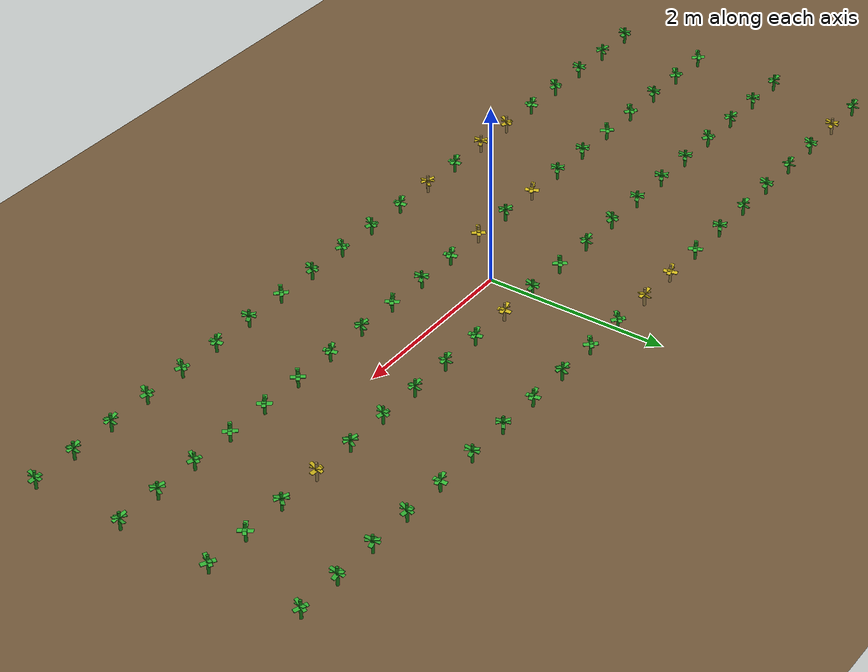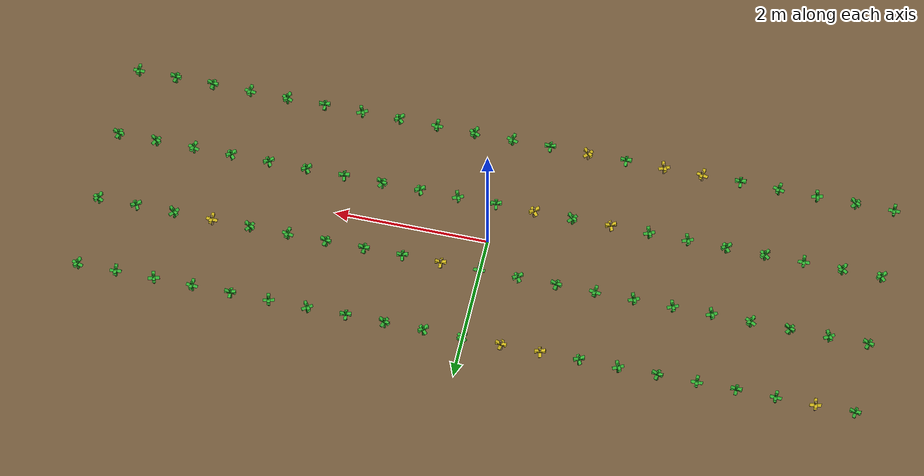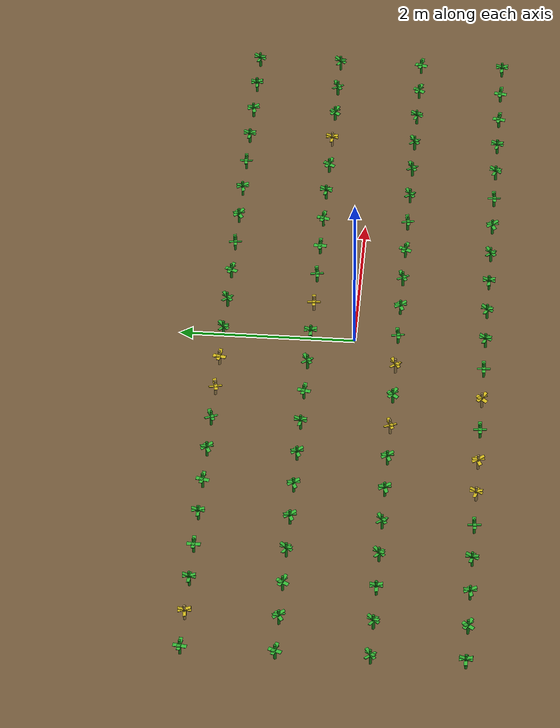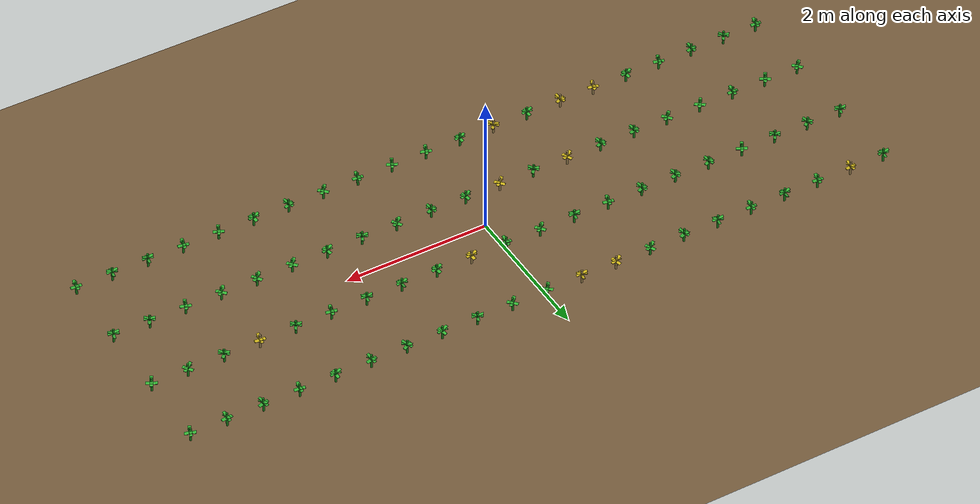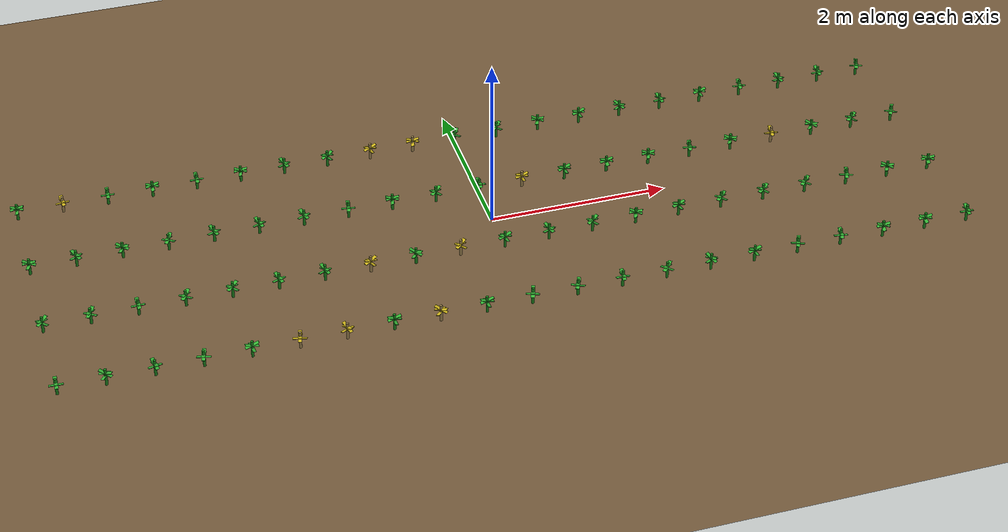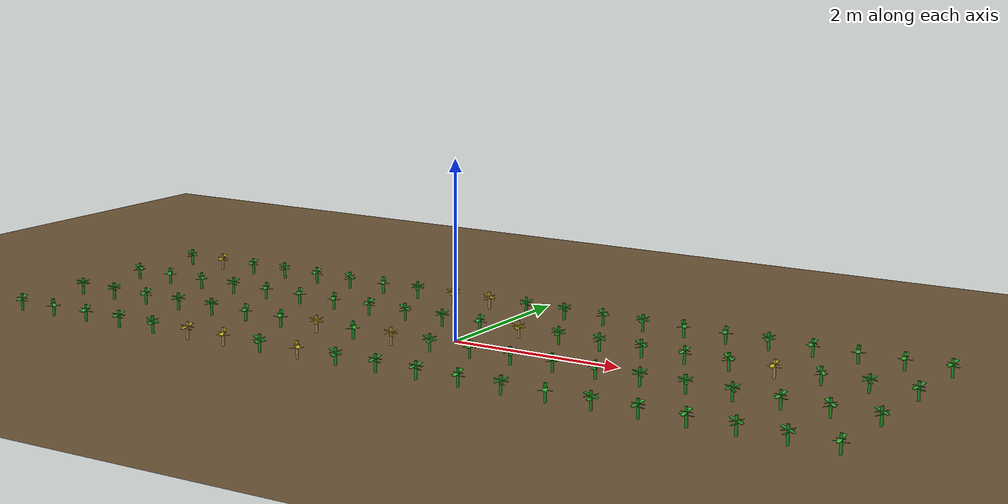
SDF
<?xml version='1.0'?>
<sdf version='1.6'>
  <world name='farm_world'>
    <gravity>0 0 -9.8</gravity>
    <physics type='ode'>
      <real_time_update_rate>1000</real_time_update_rate>
      <max_step_size>0.001</max_step_size>
    </physics>

    <!-- Sun -->
    <include>
      <uri>model://sun</uri>
    </include>

    <!-- Brown Soil Ground -->
    <model name="soil_ground">
      <static>true</static>
      <link name="link">
        <collision name="collision">
          <geometry>
            <plane>
              <normal>0 0 1</normal>
              <size>100 100</size>
            </plane>
          </geometry>
          <surface>
            <friction>
              <ode>
                <mu>100</mu>
                <mu2>50</mu2>
              </ode>
            </friction>
          </surface>
        </collision>
        <visual name="visual">
          <cast_shadows>false</cast_shadows>
          <geometry>
            <plane>
              <normal>0 0 1</normal>
              <size>100 100</size>
            </plane>
          </geometry>
          <material>
            <script>
              <uri>file://media/materials/scripts/gazebo.material</uri>
              <name>Gazebo/Mud</name>
            </script>
            <!-- Fallback color if texture fails -->
            <ambient>0.45 0.35 0.23 1</ambient>
            <diffuse>0.45 0.35 0.23 1</diffuse>
          </material>
        </visual>
      </link>
    </model>

    <model name='plant_0'>
      <pose>-5.0 -1.5 0 0 0 1.5404168390073285</pose>
      <static>true</static>
      <link name='link'>
        <!-- Stem -->
        <visual name='stem'>
          <pose>0 0 0.1 0 0 0</pose>
          <geometry>
            <cylinder>
                <radius>0.015</radius>
                <length>0.2</length>
            </cylinder>
          </geometry>
          <material>
            <ambient>0.1 0.5 0.1 1</ambient>
            <diffuse>0.1 0.5 0.1 1</diffuse>
          </material>
        </visual>

        <!-- Leaves (Crossed Planes) -->
        <visual name='leaf_1'>
          <pose>0 0 0.15 0 0.3 0</pose>
          <geometry>
            <box><size>0.15 0.04 0.005</size></box>
          </geometry>
          <material>
             <ambient>0.2 0.7 0.2 1</ambient>
             <diffuse>0.2 0.7 0.2 1</diffuse>
          </material>
        </visual>
         <visual name='leaf_2'>
          <pose>0 0 0.15 0 -0.3 0</pose>
          <geometry>
            <box><size>0.15 0.04 0.005</size></box>
          </geometry>
          <material>
             <ambient>0.2 0.7 0.2 1</ambient>
             <diffuse>0.2 0.7 0.2 1</diffuse>
          </material>
        </visual>
         <visual name='leaf_3'>
          <pose>0 0 0.12 0.3 0 1.57</pose>
          <geometry>
            <box><size>0.15 0.04 0.005</size></box>
          </geometry>
          <material>
             <ambient>0.2 0.7 0.2 1</ambient>
             <diffuse>0.2 0.7 0.2 1</diffuse>
          </material>
        </visual>

        <collision name='collision'>
          <pose>0 0 0.1 0 0 0</pose>
          <geometry>
             <cylinder>
                <radius>0.05</radius>
                <length>0.2</length>
            </cylinder>
          </geometry>
        </collision>
      </link>
    </model>

    <model name='plant_1'>
      <pose>-5.0 -0.5 0 0 0 0.7351453791681434</pose>
      <static>true</static>
      <link name='link'>
        <!-- Stem -->
        <visual name='stem'>
          <pose>0 0 0.1 0 0 0</pose>
          <geometry>
            <cylinder>
                <radius>0.015</radius>
                <length>0.2</length>
            </cylinder>
          </geometry>
          <material>
            <ambient>0.1 0.5 0.1 1</ambient>
            <diffuse>0.1 0.5 0.1 1</diffuse>
          </material>
        </visual>

        <!-- Leaves (Crossed Planes) -->
        <visual name='leaf_1'>
          <pose>0 0 0.15 0 0.3 0</pose>
          <geometry>
            <box><size>0.15 0.04 0.005</size></box>
          </geometry>
          <material>
             <ambient>0.2 0.7 0.2 1</ambient>
             <diffuse>0.2 0.7 0.2 1</diffuse>
          </material>
        </visual>
         <visual name='leaf_2'>
          <pose>0 0 0.15 0 -0.3 0</pose>
          <geometry>
            <box><size>0.15 0.04 0.005</size></box>
          </geometry>
          <material>
             <ambient>0.2 0.7 0.2 1</ambient>
             <diffuse>0.2 0.7 0.2 1</diffuse>
          </material>
        </visual>
         <visual name='leaf_3'>
          <pose>0 0 0.12 0.3 0 1.57</pose>
          <geometry>
            <box><size>0.15 0.04 0.005</size></box>
          </geometry>
          <material>
             <ambient>0.2 0.7 0.2 1</ambient>
             <diffuse>0.2 0.7 0.2 1</diffuse>
          </material>
        </visual>

        <collision name='collision'>
          <pose>0 0 0.1 0 0 0</pose>
          <geometry>
             <cylinder>
                <radius>0.05</radius>
                <length>0.2</length>
            </cylinder>
          </geometry>
        </collision>
      </link>
    </model>

    <model name='plant_2'>
      <pose>-5.0 0.5 0 0 0 2.8004936058000003</pose>
      <static>true</static>
      <link name='link'>
        <!-- Stem -->
        <visual name='stem'>
          <pose>0 0 0.1 0 0 0</pose>
          <geometry>
            <cylinder>
                <radius>0.015</radius>
                <length>0.2</length>
            </cylinder>
          </geometry>
          <material>
            <ambient>0.1 0.5 0.1 1</ambient>
            <diffuse>0.1 0.5 0.1 1</diffuse>
          </material>
        </visual>

        <!-- Leaves (Crossed Planes) -->
        <visual name='leaf_1'>
          <pose>0 0 0.15 0 0.3 0</pose>
          <geometry>
            <box><size>0.15 0.04 0.005</size></box>
          </geometry>
          <material>
             <ambient>0.2 0.7 0.2 1</ambient>
             <diffuse>0.2 0.7 0.2 1</diffuse>
          </material>
        </visual>
         <visual name='leaf_2'>
          <pose>0 0 0.15 0 -0.3 0</pose>
          <geometry>
            <box><size>0.15 0.04 0.005</size></box>
          </geometry>
          <material>
             <ambient>0.2 0.7 0.2 1</ambient>
             <diffuse>0.2 0.7 0.2 1</diffuse>
          </material>
        </visual>
         <visual name='leaf_3'>
          <pose>0 0 0.12 0.3 0 1.57</pose>
          <geometry>
            <box><size>0.15 0.04 0.005</size></box>
          </geometry>
          <material>
             <ambient>0.2 0.7 0.2 1</ambient>
             <diffuse>0.2 0.7 0.2 1</diffuse>
          </material>
        </visual>

        <collision name='collision'>
          <pose>0 0 0.1 0 0 0</pose>
          <geometry>
             <cylinder>
                <radius>0.05</radius>
                <length>0.2</length>
            </cylinder>
          </geometry>
        </collision>
      </link>
    </model>

    <model name='plant_3'>
      <pose>-5.0 1.5 0 0 0 2.9955637637239656</pose>
      <static>true</static>
      <link name='link'>
        <!-- Stem -->
        <visual name='stem'>
          <pose>0 0 0.1 0 0 0</pose>
          <geometry>
            <cylinder>
                <radius>0.015</radius>
                <length>0.2</length>
            </cylinder>
          </geometry>
          <material>
            <ambient>0.1 0.5 0.1 1</ambient>
            <diffuse>0.1 0.5 0.1 1</diffuse>
          </material>
        </visual>

        <!-- Leaves (Crossed Planes) -->
        <visual name='leaf_1'>
          <pose>0 0 0.15 0 0.3 0</pose>
          <geometry>
            <box><size>0.15 0.04 0.005</size></box>
          </geometry>
          <material>
             <ambient>0.2 0.7 0.2 1</ambient>
             <diffuse>0.2 0.7 0.2 1</diffuse>
          </material>
        </visual>
         <visual name='leaf_2'>
          <pose>0 0 0.15 0 -0.3 0</pose>
          <geometry>
            <box><size>0.15 0.04 0.005</size></box>
          </geometry>
          <material>
             <ambient>0.2 0.7 0.2 1</ambient>
             <diffuse>0.2 0.7 0.2 1</diffuse>
          </material>
        </visual>
         <visual name='leaf_3'>
          <pose>0 0 0.12 0.3 0 1.57</pose>
          <geometry>
            <box><size>0.15 0.04 0.005</size></box>
          </geometry>
          <material>
             <ambient>0.2 0.7 0.2 1</ambient>
             <diffuse>0.2 0.7 0.2 1</diffuse>
          </material>
        </visual>

        <collision name='collision'>
          <pose>0 0 0.1 0 0 0</pose>
          <geometry>
             <cylinder>
                <radius>0.05</radius>
                <length>0.2</length>
            </cylinder>
          </geometry>
        </collision>
      </link>
    </model>

    <model name='plant_4'>
      <pose>-4.5 -1.5 0 0 0 2.505541312539062</pose>
      <static>true</static>
      <link name='link'>
        <!-- Stem -->
        <visual name='stem'>
          <pose>0 0 0.1 0 0 0</pose>
          <geometry>
            <cylinder>
                <radius>0.015</radius>
                <length>0.2</length>
            </cylinder>
          </geometry>
          <material>
            <ambient>0.1 0.5 0.1 1</ambient>
            <diffuse>0.1 0.5 0.1 1</diffuse>
          </material>
        </visual>

        <!-- Leaves (Crossed Planes) -->
        <visual name='leaf_1'>
          <pose>0 0 0.15 0 0.3 0</pose>
          <geometry>
            <box><size>0.15 0.04 0.005</size></box>
          </geometry>
          <material>
             <ambient>0.2 0.7 0.2 1</ambient>
             <diffuse>0.2 0.7 0.2 1</diffuse>
          </material>
        </visual>
         <visual name='leaf_2'>
          <pose>0 0 0.15 0 -0.3 0</pose>
          <geometry>
            <box><size>0.15 0.04 0.005</size></box>
          </geometry>
          <material>
             <ambient>0.2 0.7 0.2 1</ambient>
             <diffuse>0.2 0.7 0.2 1</diffuse>
          </material>
        </visual>
         <visual name='leaf_3'>
          <pose>0 0 0.12 0.3 0 1.57</pose>
          <geometry>
            <box><size>0.15 0.04 0.005</size></box>
          </geometry>
          <material>
             <ambient>0.2 0.7 0.2 1</ambient>
             <diffuse>0.2 0.7 0.2 1</diffuse>
          </material>
        </visual>

        <collision name='collision'>
          <pose>0 0 0.1 0 0 0</pose>
          <geometry>
             <cylinder>
                <radius>0.05</radius>
                <length>0.2</length>
            </cylinder>
          </geometry>
        </collision>
      </link>
    </model>

    <model name='plant_5'>
      <pose>-4.5 -0.5 0 0 0 1.0031131464619787</pose>
      <static>true</static>
      <link name='link'>
        <!-- Stem -->
        <visual name='stem'>
          <pose>0 0 0.1 0 0 0</pose>
          <geometry>
            <cylinder>
                <radius>0.015</radius>
                <length>0.2</length>
            </cylinder>
          </geometry>
          <material>
            <ambient>0.1 0.5 0.1 1</ambient>
            <diffuse>0.1 0.5 0.1 1</diffuse>
          </material>
        </visual>

        <!-- Leaves (Crossed Planes) -->
        <visual name='leaf_1'>
          <pose>0 0 0.15 0 0.3 0</pose>
          <geometry>
            <box><size>0.15 0.04 0.005</size></box>
          </geometry>
          <material>
             <ambient>0.2 0.7 0.2 1</ambient>
             <diffuse>0.2 0.7 0.2 1</diffuse>
          </material>
        </visual>
         <visual name='leaf_2'>
          <pose>0 0 0.15 0 -0.3 0</pose>
          <geometry>
            <box><size>0.15 0.04 0.005</size></box>
          </geometry>
          <material>
             <ambient>0.2 0.7 0.2 1</ambient>
             <diffuse>0.2 0.7 0.2 1</diffuse>
          </material>
        </visual>
         <visual name='leaf_3'>
          <pose>0 0 0.12 0.3 0 1.57</pose>
          <geometry>
            <box><size>0.15 0.04 0.005</size></box>
          </geometry>
          <material>
             <ambient>0.2 0.7 0.2 1</ambient>
             <diffuse>0.2 0.7 0.2 1</diffuse>
          </material>
        </visual>

        <collision name='collision'>
          <pose>0 0 0.1 0 0 0</pose>
          <geometry>
             <cylinder>
                <radius>0.05</radius>
                <length>0.2</length>
            </cylinder>
          </geometry>
        </collision>
      </link>
    </model>

    <model name='plant_6'>
      <pose>-4.5 0.5 0 0 0 2.116446259178795</pose>
      <static>true</static>
      <link name='link'>
        <!-- Stem -->
        <visual name='stem'>
          <pose>0 0 0.1 0 0 0</pose>
          <geometry>
            <cylinder>
                <radius>0.015</radius>
                <length>0.2</length>
            </cylinder>
          </geometry>
          <material>
            <ambient>0.1 0.5 0.1 1</ambient>
            <diffuse>0.1 0.5 0.1 1</diffuse>
          </material>
        </visual>

        <!-- Leaves (Crossed Planes) -->
        <visual name='leaf_1'>
          <pose>0 0 0.15 0 0.3 0</pose>
          <geometry>
            <box><size>0.15 0.04 0.005</size></box>
          </geometry>
          <material>
             <ambient>0.2 0.7 0.2 1</ambient>
             <diffuse>0.2 0.7 0.2 1</diffuse>
          </material>
        </visual>
         <visual name='leaf_2'>
          <pose>0 0 0.15 0 -0.3 0</pose>
          <geometry>
            <box><size>0.15 0.04 0.005</size></box>
          </geometry>
          <material>
             <ambient>0.2 0.7 0.2 1</ambient>
             <diffuse>0.2 0.7 0.2 1</diffuse>
          </material>
        </visual>
         <visual name='leaf_3'>
          <pose>0 0 0.12 0.3 0 1.57</pose>
          <geometry>
            <box><size>0.15 0.04 0.005</size></box>
          </geometry>
          <material>
             <ambient>0.2 0.7 0.2 1</ambient>
             <diffuse>0.2 0.7 0.2 1</diffuse>
          </material>
        </visual>

        <collision name='collision'>
          <pose>0 0 0.1 0 0 0</pose>
          <geometry>
             <cylinder>
                <radius>0.05</radius>
                <length>0.2</length>
            </cylinder>
          </geometry>
        </collision>
      </link>
    </model>

    <model name='plant_7'>
      <pose>-4.5 1.5 0 0 0 1.6933295084793392</pose>
      <static>true</static>
      <link name='link'>
        <!-- Stem -->
        <visual name='stem'>
          <pose>0 0 0.1 0 0 0</pose>
          <geometry>
            <cylinder>
                <radius>0.015</radius>
                <length>0.2</length>
            </cylinder>
          </geometry>
          <material>
            <ambient>0.6 0.5 0.3 1</ambient>
            <diffuse>0.6 0.5 0.3 1</diffuse>
          </material>
        </visual>

        <!-- Leaves (Crossed Planes) -->
        <visual name='leaf_1'>
          <pose>0 0 0.15 0 0.3 0</pose>
          <geometry>
            <box><size>0.15 0.04 0.005</size></box>
          </geometry>
          <material>
             <ambient>0.8 0.7 0.1 1</ambient>
             <diffuse>0.8 0.7 0.1 1</diffuse>
          </material>
        </visual>
         <visual name='leaf_2'>
          <pose>0 0 0.15 0 -0.3 0</pose>
          <geometry>
            <box><size>0.15 0.04 0.005</size></box>
          </geometry>
          <material>
             <ambient>0.8 0.7 0.1 1</ambient>
             <diffuse>0.8 0.7 0.1 1</diffuse>
          </material>
        </visual>
         <visual name='leaf_3'>
          <pose>0 0 0.12 0.3 0 1.57</pose>
          <geometry>
            <box><size>0.15 0.04 0.005</size></box>
          </geometry>
          <material>
             <ambient>0.8 0.7 0.1 1</ambient>
             <diffuse>0.8 0.7 0.1 1</diffuse>
          </material>
        </visual>

        <collision name='collision'>
          <pose>0 0 0.1 0 0 0</pose>
          <geometry>
             <cylinder>
                <radius>0.05</radius>
                <length>0.2</length>
            </cylinder>
          </geometry>
        </collision>
      </link>
    </model>

    <model name='plant_8'>
      <pose>-4.0 -1.5 0 0 0 1.8031981682654712</pose>
      <static>true</static>
      <link name='link'>
        <!-- Stem -->
        <visual name='stem'>
          <pose>0 0 0.1 0 0 0</pose>
          <geometry>
            <cylinder>
                <radius>0.015</radius>
                <length>0.2</length>
            </cylinder>
          </geometry>
          <material>
            <ambient>0.1 0.5 0.1 1</ambient>
            <diffuse>0.1 0.5 0.1 1</diffuse>
          </material>
        </visual>

        <!-- Leaves (Crossed Planes) -->
        <visual name='leaf_1'>
          <pose>0 0 0.15 0 0.3 0</pose>
          <geometry>
            <box><size>0.15 0.04 0.005</size></box>
          </geometry>
          <material>
             <ambient>0.2 0.7 0.2 1</ambient>
             <diffuse>0.2 0.7 0.2 1</diffuse>
          </material>
        </visual>
         <visual name='leaf_2'>
          <pose>0 0 0.15 0 -0.3 0</pose>
          <geometry>
            <box><size>0.15 0.04 0.005</size></box>
          </geometry>
          <material>
             <ambient>0.2 0.7 0.2 1</ambient>
             <diffuse>0.2 0.7 0.2 1</diffuse>
          </material>
        </visual>
         <visual name='leaf_3'>
          <pose>0 0 0.12 0.3 0 1.57</pose>
          <geometry>
            <box><size>0.15 0.04 0.005</size></box>
          </geometry>
          <material>
             <ambient>0.2 0.7 0.2 1</ambient>
             <diffuse>0.2 0.7 0.2 1</diffuse>
          </material>
        </visual>

        <collision name='collision'>
          <pose>0 0 0.1 0 0 0</pose>
          <geometry>
             <cylinder>
                <radius>0.05</radius>
                <length>0.2</length>
            </cylinder>
          </geometry>
        </collision>
      </link>
    </model>

    <model name='plant_9'>
      <pose>-4.0 -0.5 0 0 0 1.6151997988479085</pose>
      <static>true</static>
      <link name='link'>
        <!-- Stem -->
        <visual name='stem'>
          <pose>0 0 0.1 0 0 0</pose>
          <geometry>
            <cylinder>
                <radius>0.015</radius>
                <length>0.2</length>
            </cylinder>
          </geometry>
          <material>
            <ambient>0.1 0.5 0.1 1</ambient>
            <diffuse>0.1 0.5 0.1 1</diffuse>
          </material>
        </visual>

        <!-- Leaves (Crossed Planes) -->
        <visual name='leaf_1'>
          <pose>0 0 0.15 0 0.3 0</pose>
          <geometry>
            <box><size>0.15 0.04 0.005</size></box>
          </geometry>
          <material>
             <ambient>0.2 0.7 0.2 1</ambient>
             <diffuse>0.2 0.7 0.2 1</diffuse>
          </material>
        </visual>
         <visual name='leaf_2'>
          <pose>0 0 0.15 0 -0.3 0</pose>
          <geometry>
            <box><size>0.15 0.04 0.005</size></box>
          </geometry>
          <material>
             <ambient>0.2 0.7 0.2 1</ambient>
             <diffuse>0.2 0.7 0.2 1</diffuse>
          </material>
        </visual>
         <visual name='leaf_3'>
          <pose>0 0 0.12 0.3 0 1.57</pose>
          <geometry>
            <box><size>0.15 0.04 0.005</size></box>
          </geometry>
          <material>
             <ambient>0.2 0.7 0.2 1</ambient>
             <diffuse>0.2 0.7 0.2 1</diffuse>
          </material>
        </visual>

        <collision name='collision'>
          <pose>0 0 0.1 0 0 0</pose>
          <geometry>
             <cylinder>
                <radius>0.05</radius>
                <length>0.2</length>
            </cylinder>
          </geometry>
        </collision>
      </link>
    </model>

    <model name='plant_10'>
      <pose>-4.0 0.5 0 0 0 2.603640533188964</pose>
      <static>true</static>
      <link name='link'>
        <!-- Stem -->
        <visual name='stem'>
          <pose>0 0 0.1 0 0 0</pose>
          <geometry>
            <cylinder>
                <radius>0.015</radius>
                <length>0.2</length>
            </cylinder>
          </geometry>
          <material>
            <ambient>0.1 0.5 0.1 1</ambient>
            <diffuse>0.1 0.5 0.1 1</diffuse>
          </material>
        </visual>

        <!-- Leaves (Crossed Planes) -->
        <visual name='leaf_1'>
          <pose>0 0 0.15 0 0.3 0</pose>
          <geometry>
            <box><size>0.15 0.04 0.005</size></box>
          </geometry>
          <material>
             <ambient>0.2 0.7 0.2 1</ambient>
             <diffuse>0.2 0.7 0.2 1</diffuse>
          </material>
        </visual>
         <visual name='leaf_2'>
          <pose>0 0 0.15 0 -0.3 0</pose>
          <geometry>
            <box><size>0.15 0.04 0.005</size></box>
          </geometry>
          <material>
             <ambient>0.2 0.7 0.2 1</ambient>
             <diffuse>0.2 0.7 0.2 1</diffuse>
          </material>
        </visual>
         <visual name='leaf_3'>
          <pose>0 0 0.12 0.3 0 1.57</pose>
          <geometry>
            <box><size>0.15 0.04 0.005</size></box>
          </geometry>
          <material>
             <ambient>0.2 0.7 0.2 1</ambient>
             <diffuse>0.2 0.7 0.2 1</diffuse>
          </material>
        </visual>

        <collision name='collision'>
          <pose>0 0 0.1 0 0 0</pose>
          <geometry>
             <cylinder>
                <radius>0.05</radius>
                <length>0.2</length>
            </cylinder>
          </geometry>
        </collision>
      </link>
    </model>

    <model name='plant_11'>
      <pose>-4.0 1.5 0 0 0 1.5218412216829404</pose>
      <static>true</static>
      <link name='link'>
        <!-- Stem -->
        <visual name='stem'>
          <pose>0 0 0.1 0 0 0</pose>
          <geometry>
            <cylinder>
                <radius>0.015</radius>
                <length>0.2</length>
            </cylinder>
          </geometry>
          <material>
            <ambient>0.1 0.5 0.1 1</ambient>
            <diffuse>0.1 0.5 0.1 1</diffuse>
          </material>
        </visual>

        <!-- Leaves (Crossed Planes) -->
        <visual name='leaf_1'>
          <pose>0 0 0.15 0 0.3 0</pose>
          <geometry>
            <box><size>0.15 0.04 0.005</size></box>
          </geometry>
          <material>
             <ambient>0.2 0.7 0.2 1</ambient>
             <diffuse>0.2 0.7 0.2 1</diffuse>
          </material>
        </visual>
         <visual name='leaf_2'>
          <pose>0 0 0.15 0 -0.3 0</pose>
          <geometry>
            <box><size>0.15 0.04 0.005</size></box>
          </geometry>
          <material>
             <ambient>0.2 0.7 0.2 1</ambient>
             <diffuse>0.2 0.7 0.2 1</diffuse>
          </material>
        </visual>
         <visual name='leaf_3'>
          <pose>0 0 0.12 0.3 0 1.57</pose>
          <geometry>
            <box><size>0.15 0.04 0.005</size></box>
          </geometry>
          <material>
             <ambient>0.2 0.7 0.2 1</ambient>
             <diffuse>0.2 0.7 0.2 1</diffuse>
          </material>
        </visual>

        <collision name='collision'>
          <pose>0 0 0.1 0 0 0</pose>
          <geometry>
             <cylinder>
                <radius>0.05</radius>
                <length>0.2</length>
            </cylinder>
          </geometry>
        </collision>
      </link>
    </model>

    <model name='plant_12'>
      <pose>-3.5 -1.5 0 0 0 1.3043515372291121</pose>
      <static>true</static>
      <link name='link'>
        <!-- Stem -->
        <visual name='stem'>
          <pose>0 0 0.1 0 0 0</pose>
          <geometry>
            <cylinder>
                <radius>0.015</radius>
                <length>0.2</length>
            </cylinder>
          </geometry>
          <material>
            <ambient>0.1 0.5 0.1 1</ambient>
            <diffuse>0.1 0.5 0.1 1</diffuse>
          </material>
        </visual>

        <!-- Leaves (Crossed Planes) -->
        <visual name='leaf_1'>
          <pose>0 0 0.15 0 0.3 0</pose>
          <geometry>
            <box><size>0.15 0.04 0.005</size></box>
          </geometry>
          <material>
             <ambient>0.2 0.7 0.2 1</ambient>
             <diffuse>0.2 0.7 0.2 1</diffuse>
          </material>
        </visual>
         <visual name='leaf_2'>
          <pose>0 0 0.15 0 -0.3 0</pose>
          <geometry>
            <box><size>0.15 0.04 0.005</size></box>
          </geometry>
          <material>
             <ambient>0.2 0.7 0.2 1</ambient>
             <diffuse>0.2 0.7 0.2 1</diffuse>
          </material>
        </visual>
         <visual name='leaf_3'>
          <pose>0 0 0.12 0.3 0 1.57</pose>
          <geometry>
            <box><size>0.15 0.04 0.005</size></box>
          </geometry>
          <material>
             <ambient>0.2 0.7 0.2 1</ambient>
             <diffuse>0.2 0.7 0.2 1</diffuse>
          </material>
        </visual>

        <collision name='collision'>
          <pose>0 0 0.1 0 0 0</pose>
          <geometry>
             <cylinder>
                <radius>0.05</radius>
                <length>0.2</length>
            </cylinder>
          </geometry>
        </collision>
      </link>
    </model>

    <model name='plant_13'>
      <pose>-3.5 -0.5 0 0 0 0.9241253141846406</pose>
      <static>true</static>
      <link name='link'>
        <!-- Stem -->
        <visual name='stem'>
          <pose>0 0 0.1 0 0 0</pose>
          <geometry>
            <cylinder>
                <radius>0.015</radius>
                <length>0.2</length>
            </cylinder>
          </geometry>
          <material>
            <ambient>0.1 0.5 0.1 1</ambient>
            <diffuse>0.1 0.5 0.1 1</diffuse>
          </material>
        </visual>

        <!-- Leaves (Crossed Planes) -->
        <visual name='leaf_1'>
          <pose>0 0 0.15 0 0.3 0</pose>
          <geometry>
            <box><size>0.15 0.04 0.005</size></box>
          </geometry>
          <material>
             <ambient>0.2 0.7 0.2 1</ambient>
             <diffuse>0.2 0.7 0.2 1</diffuse>
          </material>
        </visual>
         <visual name='leaf_2'>
          <pose>0 0 0.15 0 -0.3 0</pose>
          <geometry>
            <box><size>0.15 0.04 0.005</size></box>
          </geometry>
          <material>
             <ambient>0.2 0.7 0.2 1</ambient>
             <diffuse>0.2 0.7 0.2 1</diffuse>
          </material>
        </visual>
         <visual name='leaf_3'>
          <pose>0 0 0.12 0.3 0 1.57</pose>
          <geometry>
            <box><size>0.15 0.04 0.005</size></box>
          </geometry>
          <material>
             <ambient>0.2 0.7 0.2 1</ambient>
             <diffuse>0.2 0.7 0.2 1</diffuse>
          </material>
        </visual>

        <collision name='collision'>
          <pose>0 0 0.1 0 0 0</pose>
          <geometry>
             <cylinder>
                <radius>0.05</radius>
                <length>0.2</length>
            </cylinder>
          </geometry>
        </collision>
      </link>
    </model>

    <model name='plant_14'>
      <pose>-3.5 0.5 0 0 0 1.0664166804434985</pose>
      <static>true</static>
      <link name='link'>
        <!-- Stem -->
        <visual name='stem'>
          <pose>0 0 0.1 0 0 0</pose>
          <geometry>
            <cylinder>
                <radius>0.015</radius>
                <length>0.2</length>
            </cylinder>
          </geometry>
          <material>
            <ambient>0.1 0.5 0.1 1</ambient>
            <diffuse>0.1 0.5 0.1 1</diffuse>
          </material>
        </visual>

        <!-- Leaves (Crossed Planes) -->
        <visual name='leaf_1'>
          <pose>0 0 0.15 0 0.3 0</pose>
          <geometry>
            <box><size>0.15 0.04 0.005</size></box>
          </geometry>
          <material>
             <ambient>0.2 0.7 0.2 1</ambient>
             <diffuse>0.2 0.7 0.2 1</diffuse>
          </material>
        </visual>
         <visual name='leaf_2'>
          <pose>0 0 0.15 0 -0.3 0</pose>
          <geometry>
            <box><size>0.15 0.04 0.005</size></box>
          </geometry>
          <material>
             <ambient>0.2 0.7 0.2 1</ambient>
             <diffuse>0.2 0.7 0.2 1</diffuse>
          </material>
        </visual>
         <visual name='leaf_3'>
          <pose>0 0 0.12 0.3 0 1.57</pose>
          <geometry>
            <box><size>0.15 0.04 0.005</size></box>
          </geometry>
          <material>
             <ambient>0.2 0.7 0.2 1</ambient>
             <diffuse>0.2 0.7 0.2 1</diffuse>
          </material>
        </visual>

        <collision name='collision'>
          <pose>0 0 0.1 0 0 0</pose>
          <geometry>
             <cylinder>
                <radius>0.05</radius>
                <length>0.2</length>
            </cylinder>
          </geometry>
        </collision>
      </link>
    </model>

    <model name='plant_15'>
      <pose>-3.5 1.5 0 0 0 3.105797637310526</pose>
      <static>true</static>
      <link name='link'>
        <!-- Stem -->
        <visual name='stem'>
          <pose>0 0 0.1 0 0 0</pose>
          <geometry>
            <cylinder>
                <radius>0.015</radius>
                <length>0.2</length>
            </cylinder>
          </geometry>
          <material>
            <ambient>0.1 0.5 0.1 1</ambient>
            <diffuse>0.1 0.5 0.1 1</diffuse>
          </material>
        </visual>

        <!-- Leaves (Crossed Planes) -->
        <visual name='leaf_1'>
          <pose>0 0 0.15 0 0.3 0</pose>
          <geometry>
            <box><size>0.15 0.04 0.005</size></box>
          </geometry>
          <material>
             <ambient>0.2 0.7 0.2 1</ambient>
             <diffuse>0.2 0.7 0.2 1</diffuse>
          </material>
        </visual>
         <visual name='leaf_2'>
          <pose>0 0 0.15 0 -0.3 0</pose>
          <geometry>
            <box><size>0.15 0.04 0.005</size></box>
          </geometry>
          <material>
             <ambient>0.2 0.7 0.2 1</ambient>
             <diffuse>0.2 0.7 0.2 1</diffuse>
          </material>
        </visual>
         <visual name='leaf_3'>
          <pose>0 0 0.12 0.3 0 1.57</pose>
          <geometry>
            <box><size>0.15 0.04 0.005</size></box>
          </geometry>
          <material>
             <ambient>0.2 0.7 0.2 1</ambient>
             <diffuse>0.2 0.7 0.2 1</diffuse>
          </material>
        </visual>

        <collision name='collision'>
          <pose>0 0 0.1 0 0 0</pose>
          <geometry>
             <cylinder>
                <radius>0.05</radius>
                <length>0.2</length>
            </cylinder>
          </geometry>
        </collision>
      </link>
    </model>

    <model name='plant_16'>
      <pose>-3.0 -1.5 0 0 0 0.09040154062016818</pose>
      <static>true</static>
      <link name='link'>
        <!-- Stem -->
        <visual name='stem'>
          <pose>0 0 0.1 0 0 0</pose>
          <geometry>
            <cylinder>
                <radius>0.015</radius>
                <length>0.2</length>
            </cylinder>
          </geometry>
          <material>
            <ambient>0.1 0.5 0.1 1</ambient>
            <diffuse>0.1 0.5 0.1 1</diffuse>
          </material>
        </visual>

        <!-- Leaves (Crossed Planes) -->
        <visual name='leaf_1'>
          <pose>0 0 0.15 0 0.3 0</pose>
          <geometry>
            <box><size>0.15 0.04 0.005</size></box>
          </geometry>
          <material>
             <ambient>0.2 0.7 0.2 1</ambient>
             <diffuse>0.2 0.7 0.2 1</diffuse>
          </material>
        </visual>
         <visual name='leaf_2'>
          <pose>0 0 0.15 0 -0.3 0</pose>
          <geometry>
            <box><size>0.15 0.04 0.005</size></box>
          </geometry>
          <material>
             <ambient>0.2 0.7 0.2 1</ambient>
             <diffuse>0.2 0.7 0.2 1</diffuse>
          </material>
        </visual>
         <visual name='leaf_3'>
          <pose>0 0 0.12 0.3 0 1.57</pose>
          <geometry>
            <box><size>0.15 0.04 0.005</size></box>
          </geometry>
          <material>
             <ambient>0.2 0.7 0.2 1</ambient>
             <diffuse>0.2 0.7 0.2 1</diffuse>
          </material>
        </visual>

        <collision name='collision'>
          <pose>0 0 0.1 0 0 0</pose>
          <geometry>
             <cylinder>
                <radius>0.05</radius>
                <length>0.2</length>
            </cylinder>
          </geometry>
        </collision>
      </link>
    </model>

    <model name='plant_17'>
      <pose>-3.0 -0.5 0 0 0 0.6646975784411644</pose>
      <static>true</static>
      <link name='link'>
        <!-- Stem -->
        <visual name='stem'>
          <pose>0 0 0.1 0 0 0</pose>
          <geometry>
            <cylinder>
                <radius>0.015</radius>
                <length>0.2</length>
            </cylinder>
          </geometry>
          <material>
            <ambient>0.1 0.5 0.1 1</ambient>
            <diffuse>0.1 0.5 0.1 1</diffuse>
          </material>
        </visual>

        <!-- Leaves (Crossed Planes) -->
        <visual name='leaf_1'>
          <pose>0 0 0.15 0 0.3 0</pose>
          <geometry>
            <box><size>0.15 0.04 0.005</size></box>
          </geometry>
          <material>
             <ambient>0.2 0.7 0.2 1</ambient>
             <diffuse>0.2 0.7 0.2 1</diffuse>
          </material>
        </visual>
         <visual name='leaf_2'>
          <pose>0 0 0.15 0 -0.3 0</pose>
          <geometry>
            <box><size>0.15 0.04 0.005</size></box>
          </geometry>
          <material>
             <ambient>0.2 0.7 0.2 1</ambient>
             <diffuse>0.2 0.7 0.2 1</diffuse>
          </material>
        </visual>
         <visual name='leaf_3'>
          <pose>0 0 0.12 0.3 0 1.57</pose>
          <geometry>
            <box><size>0.15 0.04 0.005</size></box>
          </geometry>
          <material>
             <ambient>0.2 0.7 0.2 1</ambient>
             <diffuse>0.2 0.7 0.2 1</diffuse>
          </material>
        </visual>

        <collision name='collision'>
          <pose>0 0 0.1 0 0 0</pose>
          <geometry>
             <cylinder>
                <radius>0.05</radius>
                <length>0.2</length>
            </cylinder>
          </geometry>
        </collision>
      </link>
    </model>

    <model name='plant_18'>
      <pose>-3.0 0.5 0 0 0 1.982889856789044</pose>
      <static>true</static>
      <link name='link'>
        <!-- Stem -->
        <visual name='stem'>
          <pose>0 0 0.1 0 0 0</pose>
          <geometry>
            <cylinder>
                <radius>0.015</radius>
                <length>0.2</length>
            </cylinder>
          </geometry>
          <material>
            <ambient>0.1 0.5 0.1 1</ambient>
            <diffuse>0.1 0.5 0.1 1</diffuse>
          </material>
        </visual>

        <!-- Leaves (Crossed Planes) -->
        <visual name='leaf_1'>
          <pose>0 0 0.15 0 0.3 0</pose>
          <geometry>
            <box><size>0.15 0.04 0.005</size></box>
          </geometry>
          <material>
             <ambient>0.2 0.7 0.2 1</ambient>
             <diffuse>0.2 0.7 0.2 1</diffuse>
          </material>
        </visual>
         <visual name='leaf_2'>
          <pose>0 0 0.15 0 -0.3 0</pose>
          <geometry>
            <box><size>0.15 0.04 0.005</size></box>
          </geometry>
          <material>
             <ambient>0.2 0.7 0.2 1</ambient>
             <diffuse>0.2 0.7 0.2 1</diffuse>
          </material>
        </visual>
         <visual name='leaf_3'>
          <pose>0 0 0.12 0.3 0 1.57</pose>
          <geometry>
            <box><size>0.15 0.04 0.005</size></box>
          </geometry>
          <material>
             <ambient>0.2 0.7 0.2 1</ambient>
             <diffuse>0.2 0.7 0.2 1</diffuse>
          </material>
        </visual>

        <collision name='collision'>
          <pose>0 0 0.1 0 0 0</pose>
          <geometry>
             <cylinder>
                <radius>0.05</radius>
                <length>0.2</length>
            </cylinder>
          </geometry>
        </collision>
      </link>
    </model>

    <model name='plant_19'>
      <pose>-3.0 1.5 0 0 0 1.579053686544608</pose>
      <static>true</static>
      <link name='link'>
        <!-- Stem -->
        <visual name='stem'>
          <pose>0 0 0.1 0 0 0</pose>
          <geometry>
            <cylinder>
                <radius>0.015</radius>
                <length>0.2</length>
            </cylinder>
          </geometry>
          <material>
            <ambient>0.1 0.5 0.1 1</ambient>
            <diffuse>0.1 0.5 0.1 1</diffuse>
          </material>
        </visual>

        <!-- Leaves (Crossed Planes) -->
        <visual name='leaf_1'>
          <pose>0 0 0.15 0 0.3 0</pose>
          <geometry>
            <box><size>0.15 0.04 0.005</size></box>
          </geometry>
          <material>
             <ambient>0.2 0.7 0.2 1</ambient>
             <diffuse>0.2 0.7 0.2 1</diffuse>
          </material>
        </visual>
         <visual name='leaf_2'>
          <pose>0 0 0.15 0 -0.3 0</pose>
          <geometry>
            <box><size>0.15 0.04 0.005</size></box>
          </geometry>
          <material>
             <ambient>0.2 0.7 0.2 1</ambient>
             <diffuse>0.2 0.7 0.2 1</diffuse>
          </material>
        </visual>
         <visual name='leaf_3'>
          <pose>0 0 0.12 0.3 0 1.57</pose>
          <geometry>
            <box><size>0.15 0.04 0.005</size></box>
          </geometry>
          <material>
             <ambient>0.2 0.7 0.2 1</ambient>
             <diffuse>0.2 0.7 0.2 1</diffuse>
          </material>
        </visual>

        <collision name='collision'>
          <pose>0 0 0.1 0 0 0</pose>
          <geometry>
             <cylinder>
                <radius>0.05</radius>
                <length>0.2</length>
            </cylinder>
          </geometry>
        </collision>
      </link>
    </model>

    <model name='plant_20'>
      <pose>-2.5 -1.5 0 0 0 1.3337662383668074</pose>
      <static>true</static>
      <link name='link'>
        <!-- Stem -->
        <visual name='stem'>
          <pose>0 0 0.1 0 0 0</pose>
          <geometry>
            <cylinder>
                <radius>0.015</radius>
                <length>0.2</length>
            </cylinder>
          </geometry>
          <material>
            <ambient>0.6 0.5 0.3 1</ambient>
            <diffuse>0.6 0.5 0.3 1</diffuse>
          </material>
        </visual>

        <!-- Leaves (Crossed Planes) -->
        <visual name='leaf_1'>
          <pose>0 0 0.15 0 0.3 0</pose>
          <geometry>
            <box><size>0.15 0.04 0.005</size></box>
          </geometry>
          <material>
             <ambient>0.8 0.7 0.1 1</ambient>
             <diffuse>0.8 0.7 0.1 1</diffuse>
          </material>
        </visual>
         <visual name='leaf_2'>
          <pose>0 0 0.15 0 -0.3 0</pose>
          <geometry>
            <box><size>0.15 0.04 0.005</size></box>
          </geometry>
          <material>
             <ambient>0.8 0.7 0.1 1</ambient>
             <diffuse>0.8 0.7 0.1 1</diffuse>
          </material>
        </visual>
         <visual name='leaf_3'>
          <pose>0 0 0.12 0.3 0 1.57</pose>
          <geometry>
            <box><size>0.15 0.04 0.005</size></box>
          </geometry>
          <material>
             <ambient>0.8 0.7 0.1 1</ambient>
             <diffuse>0.8 0.7 0.1 1</diffuse>
          </material>
        </visual>

        <collision name='collision'>
          <pose>0 0 0.1 0 0 0</pose>
          <geometry>
             <cylinder>
                <radius>0.05</radius>
                <length>0.2</length>
            </cylinder>
          </geometry>
        </collision>
      </link>
    </model>

    <model name='plant_21'>
      <pose>-2.5 -0.5 0 0 0 1.9403929562869273</pose>
      <static>true</static>
      <link name='link'>
        <!-- Stem -->
        <visual name='stem'>
          <pose>0 0 0.1 0 0 0</pose>
          <geometry>
            <cylinder>
                <radius>0.015</radius>
                <length>0.2</length>
            </cylinder>
          </geometry>
          <material>
            <ambient>0.1 0.5 0.1 1</ambient>
            <diffuse>0.1 0.5 0.1 1</diffuse>
          </material>
        </visual>

        <!-- Leaves (Crossed Planes) -->
        <visual name='leaf_1'>
          <pose>0 0 0.15 0 0.3 0</pose>
          <geometry>
            <box><size>0.15 0.04 0.005</size></box>
          </geometry>
          <material>
             <ambient>0.2 0.7 0.2 1</ambient>
             <diffuse>0.2 0.7 0.2 1</diffuse>
          </material>
        </visual>
         <visual name='leaf_2'>
          <pose>0 0 0.15 0 -0.3 0</pose>
          <geometry>
            <box><size>0.15 0.04 0.005</size></box>
          </geometry>
          <material>
             <ambient>0.2 0.7 0.2 1</ambient>
             <diffuse>0.2 0.7 0.2 1</diffuse>
          </material>
        </visual>
         <visual name='leaf_3'>
          <pose>0 0 0.12 0.3 0 1.57</pose>
          <geometry>
            <box><size>0.15 0.04 0.005</size></box>
          </geometry>
          <material>
             <ambient>0.2 0.7 0.2 1</ambient>
             <diffuse>0.2 0.7 0.2 1</diffuse>
          </material>
        </visual>

        <collision name='collision'>
          <pose>0 0 0.1 0 0 0</pose>
          <geometry>
             <cylinder>
                <radius>0.05</radius>
                <length>0.2</length>
            </cylinder>
          </geometry>
        </collision>
      </link>
    </model>

    <model name='plant_22'>
      <pose>-2.5 0.5 0 0 0 1.970003988450443</pose>
      <static>true</static>
      <link name='link'>
        <!-- Stem -->
        <visual name='stem'>
          <pose>0 0 0.1 0 0 0</pose>
          <geometry>
            <cylinder>
                <radius>0.015</radius>
                <length>0.2</length>
            </cylinder>
          </geometry>
          <material>
            <ambient>0.1 0.5 0.1 1</ambient>
            <diffuse>0.1 0.5 0.1 1</diffuse>
          </material>
        </visual>

        <!-- Leaves (Crossed Planes) -->
        <visual name='leaf_1'>
          <pose>0 0 0.15 0 0.3 0</pose>
          <geometry>
            <box><size>0.15 0.04 0.005</size></box>
          </geometry>
          <material>
             <ambient>0.2 0.7 0.2 1</ambient>
             <diffuse>0.2 0.7 0.2 1</diffuse>
          </material>
        </visual>
         <visual name='leaf_2'>
          <pose>0 0 0.15 0 -0.3 0</pose>
          <geometry>
            <box><size>0.15 0.04 0.005</size></box>
          </geometry>
          <material>
             <ambient>0.2 0.7 0.2 1</ambient>
             <diffuse>0.2 0.7 0.2 1</diffuse>
          </material>
        </visual>
         <visual name='leaf_3'>
          <pose>0 0 0.12 0.3 0 1.57</pose>
          <geometry>
            <box><size>0.15 0.04 0.005</size></box>
          </geometry>
          <material>
             <ambient>0.2 0.7 0.2 1</ambient>
             <diffuse>0.2 0.7 0.2 1</diffuse>
          </material>
        </visual>

        <collision name='collision'>
          <pose>0 0 0.1 0 0 0</pose>
          <geometry>
             <cylinder>
                <radius>0.05</radius>
                <length>0.2</length>
            </cylinder>
          </geometry>
        </collision>
      </link>
    </model>

    <model name='plant_23'>
      <pose>-2.5 1.5 0 0 0 2.919846343021628</pose>
      <static>true</static>
      <link name='link'>
        <!-- Stem -->
        <visual name='stem'>
          <pose>0 0 0.1 0 0 0</pose>
          <geometry>
            <cylinder>
                <radius>0.015</radius>
                <length>0.2</length>
            </cylinder>
          </geometry>
          <material>
            <ambient>0.1 0.5 0.1 1</ambient>
            <diffuse>0.1 0.5 0.1 1</diffuse>
          </material>
        </visual>

        <!-- Leaves (Crossed Planes) -->
        <visual name='leaf_1'>
          <pose>0 0 0.15 0 0.3 0</pose>
          <geometry>
            <box><size>0.15 0.04 0.005</size></box>
          </geometry>
          <material>
             <ambient>0.2 0.7 0.2 1</ambient>
             <diffuse>0.2 0.7 0.2 1</diffuse>
          </material>
        </visual>
         <visual name='leaf_2'>
          <pose>0 0 0.15 0 -0.3 0</pose>
          <geometry>
            <box><size>0.15 0.04 0.005</size></box>
          </geometry>
          <material>
             <ambient>0.2 0.7 0.2 1</ambient>
             <diffuse>0.2 0.7 0.2 1</diffuse>
          </material>
        </visual>
         <visual name='leaf_3'>
          <pose>0 0 0.12 0.3 0 1.57</pose>
          <geometry>
            <box><size>0.15 0.04 0.005</size></box>
          </geometry>
          <material>
             <ambient>0.2 0.7 0.2 1</ambient>
             <diffuse>0.2 0.7 0.2 1</diffuse>
          </material>
        </visual>

        <collision name='collision'>
          <pose>0 0 0.1 0 0 0</pose>
          <geometry>
             <cylinder>
                <radius>0.05</radius>
                <length>0.2</length>
            </cylinder>
          </geometry>
        </collision>
      </link>
    </model>

    <model name='plant_24'>
      <pose>-2.0 -1.5 0 0 0 1.9707146502493647</pose>
      <static>true</static>
      <link name='link'>
        <!-- Stem -->
        <visual name='stem'>
          <pose>0 0 0.1 0 0 0</pose>
          <geometry>
            <cylinder>
                <radius>0.015</radius>
                <length>0.2</length>
            </cylinder>
          </geometry>
          <material>
            <ambient>0.6 0.5 0.3 1</ambient>
            <diffuse>0.6 0.5 0.3 1</diffuse>
          </material>
        </visual>

        <!-- Leaves (Crossed Planes) -->
        <visual name='leaf_1'>
          <pose>0 0 0.15 0 0.3 0</pose>
          <geometry>
            <box><size>0.15 0.04 0.005</size></box>
          </geometry>
          <material>
             <ambient>0.8 0.7 0.1 1</ambient>
             <diffuse>0.8 0.7 0.1 1</diffuse>
          </material>
        </visual>
         <visual name='leaf_2'>
          <pose>0 0 0.15 0 -0.3 0</pose>
          <geometry>
            <box><size>0.15 0.04 0.005</size></box>
          </geometry>
          <material>
             <ambient>0.8 0.7 0.1 1</ambient>
             <diffuse>0.8 0.7 0.1 1</diffuse>
          </material>
        </visual>
         <visual name='leaf_3'>
          <pose>0 0 0.12 0.3 0 1.57</pose>
          <geometry>
            <box><size>0.15 0.04 0.005</size></box>
          </geometry>
          <material>
             <ambient>0.8 0.7 0.1 1</ambient>
             <diffuse>0.8 0.7 0.1 1</diffuse>
          </material>
        </visual>

        <collision name='collision'>
          <pose>0 0 0.1 0 0 0</pose>
          <geometry>
             <cylinder>
                <radius>0.05</radius>
                <length>0.2</length>
            </cylinder>
          </geometry>
        </collision>
      </link>
    </model>

    <model name='plant_25'>
      <pose>-2.0 -0.5 0 0 0 1.9866814000168205</pose>
      <static>true</static>
      <link name='link'>
        <!-- Stem -->
        <visual name='stem'>
          <pose>0 0 0.1 0 0 0</pose>
          <geometry>
            <cylinder>
                <radius>0.015</radius>
                <length>0.2</length>
            </cylinder>
          </geometry>
          <material>
            <ambient>0.1 0.5 0.1 1</ambient>
            <diffuse>0.1 0.5 0.1 1</diffuse>
          </material>
        </visual>

        <!-- Leaves (Crossed Planes) -->
        <visual name='leaf_1'>
          <pose>0 0 0.15 0 0.3 0</pose>
          <geometry>
            <box><size>0.15 0.04 0.005</size></box>
          </geometry>
          <material>
             <ambient>0.2 0.7 0.2 1</ambient>
             <diffuse>0.2 0.7 0.2 1</diffuse>
          </material>
        </visual>
         <visual name='leaf_2'>
          <pose>0 0 0.15 0 -0.3 0</pose>
          <geometry>
            <box><size>0.15 0.04 0.005</size></box>
          </geometry>
          <material>
             <ambient>0.2 0.7 0.2 1</ambient>
             <diffuse>0.2 0.7 0.2 1</diffuse>
          </material>
        </visual>
         <visual name='leaf_3'>
          <pose>0 0 0.12 0.3 0 1.57</pose>
          <geometry>
            <box><size>0.15 0.04 0.005</size></box>
          </geometry>
          <material>
             <ambient>0.2 0.7 0.2 1</ambient>
             <diffuse>0.2 0.7 0.2 1</diffuse>
          </material>
        </visual>

        <collision name='collision'>
          <pose>0 0 0.1 0 0 0</pose>
          <geometry>
             <cylinder>
                <radius>0.05</radius>
                <length>0.2</length>
            </cylinder>
          </geometry>
        </collision>
      </link>
    </model>

    <model name='plant_26'>
      <pose>-2.0 0.5 0 0 0 1.9910888334641765</pose>
      <static>true</static>
      <link name='link'>
        <!-- Stem -->
        <visual name='stem'>
          <pose>0 0 0.1 0 0 0</pose>
          <geometry>
            <cylinder>
                <radius>0.015</radius>
                <length>0.2</length>
            </cylinder>
          </geometry>
          <material>
            <ambient>0.1 0.5 0.1 1</ambient>
            <diffuse>0.1 0.5 0.1 1</diffuse>
          </material>
        </visual>

        <!-- Leaves (Crossed Planes) -->
        <visual name='leaf_1'>
          <pose>0 0 0.15 0 0.3 0</pose>
          <geometry>
            <box><size>0.15 0.04 0.005</size></box>
          </geometry>
          <material>
             <ambient>0.2 0.7 0.2 1</ambient>
             <diffuse>0.2 0.7 0.2 1</diffuse>
          </material>
        </visual>
         <visual name='leaf_2'>
          <pose>0 0 0.15 0 -0.3 0</pose>
          <geometry>
            <box><size>0.15 0.04 0.005</size></box>
          </geometry>
          <material>
             <ambient>0.2 0.7 0.2 1</ambient>
             <diffuse>0.2 0.7 0.2 1</diffuse>
          </material>
        </visual>
         <visual name='leaf_3'>
          <pose>0 0 0.12 0.3 0 1.57</pose>
          <geometry>
            <box><size>0.15 0.04 0.005</size></box>
          </geometry>
          <material>
             <ambient>0.2 0.7 0.2 1</ambient>
             <diffuse>0.2 0.7 0.2 1</diffuse>
          </material>
        </visual>

        <collision name='collision'>
          <pose>0 0 0.1 0 0 0</pose>
          <geometry>
             <cylinder>
                <radius>0.05</radius>
                <length>0.2</length>
            </cylinder>
          </geometry>
        </collision>
      </link>
    </model>

    <model name='plant_27'>
      <pose>-2.0 1.5 0 0 0 2.036558705177706</pose>
      <static>true</static>
      <link name='link'>
        <!-- Stem -->
        <visual name='stem'>
          <pose>0 0 0.1 0 0 0</pose>
          <geometry>
            <cylinder>
                <radius>0.015</radius>
                <length>0.2</length>
            </cylinder>
          </geometry>
          <material>
            <ambient>0.1 0.5 0.1 1</ambient>
            <diffuse>0.1 0.5 0.1 1</diffuse>
          </material>
        </visual>

        <!-- Leaves (Crossed Planes) -->
        <visual name='leaf_1'>
          <pose>0 0 0.15 0 0.3 0</pose>
          <geometry>
            <box><size>0.15 0.04 0.005</size></box>
          </geometry>
          <material>
             <ambient>0.2 0.7 0.2 1</ambient>
             <diffuse>0.2 0.7 0.2 1</diffuse>
          </material>
        </visual>
         <visual name='leaf_2'>
          <pose>0 0 0.15 0 -0.3 0</pose>
          <geometry>
            <box><size>0.15 0.04 0.005</size></box>
          </geometry>
          <material>
             <ambient>0.2 0.7 0.2 1</ambient>
             <diffuse>0.2 0.7 0.2 1</diffuse>
          </material>
        </visual>
         <visual name='leaf_3'>
          <pose>0 0 0.12 0.3 0 1.57</pose>
          <geometry>
            <box><size>0.15 0.04 0.005</size></box>
          </geometry>
          <material>
             <ambient>0.2 0.7 0.2 1</ambient>
             <diffuse>0.2 0.7 0.2 1</diffuse>
          </material>
        </visual>

        <collision name='collision'>
          <pose>0 0 0.1 0 0 0</pose>
          <geometry>
             <cylinder>
                <radius>0.05</radius>
                <length>0.2</length>
            </cylinder>
          </geometry>
        </collision>
      </link>
    </model>

    <model name='plant_28'>
      <pose>-1.5 -1.5 0 0 0 0.03999692535958256</pose>
      <static>true</static>
      <link name='link'>
        <!-- Stem -->
        <visual name='stem'>
          <pose>0 0 0.1 0 0 0</pose>
          <geometry>
            <cylinder>
                <radius>0.015</radius>
                <length>0.2</length>
            </cylinder>
          </geometry>
          <material>
            <ambient>0.1 0.5 0.1 1</ambient>
            <diffuse>0.1 0.5 0.1 1</diffuse>
          </material>
        </visual>

        <!-- Leaves (Crossed Planes) -->
        <visual name='leaf_1'>
          <pose>0 0 0.15 0 0.3 0</pose>
          <geometry>
            <box><size>0.15 0.04 0.005</size></box>
          </geometry>
          <material>
             <ambient>0.2 0.7 0.2 1</ambient>
             <diffuse>0.2 0.7 0.2 1</diffuse>
          </material>
        </visual>
         <visual name='leaf_2'>
          <pose>0 0 0.15 0 -0.3 0</pose>
          <geometry>
            <box><size>0.15 0.04 0.005</size></box>
          </geometry>
          <material>
             <ambient>0.2 0.7 0.2 1</ambient>
             <diffuse>0.2 0.7 0.2 1</diffuse>
          </material>
        </visual>
         <visual name='leaf_3'>
          <pose>0 0 0.12 0.3 0 1.57</pose>
          <geometry>
            <box><size>0.15 0.04 0.005</size></box>
          </geometry>
          <material>
             <ambient>0.2 0.7 0.2 1</ambient>
             <diffuse>0.2 0.7 0.2 1</diffuse>
          </material>
        </visual>

        <collision name='collision'>
          <pose>0 0 0.1 0 0 0</pose>
          <geometry>
             <cylinder>
                <radius>0.05</radius>
                <length>0.2</length>
            </cylinder>
          </geometry>
        </collision>
      </link>
    </model>

    <model name='plant_29'>
      <pose>-1.5 -0.5 0 0 0 0.40158374649407036</pose>
      <static>true</static>
      <link name='link'>
        <!-- Stem -->
        <visual name='stem'>
          <pose>0 0 0.1 0 0 0</pose>
          <geometry>
            <cylinder>
                <radius>0.015</radius>
                <length>0.2</length>
            </cylinder>
          </geometry>
          <material>
            <ambient>0.6 0.5 0.3 1</ambient>
            <diffuse>0.6 0.5 0.3 1</diffuse>
          </material>
        </visual>

        <!-- Leaves (Crossed Planes) -->
        <visual name='leaf_1'>
          <pose>0 0 0.15 0 0.3 0</pose>
          <geometry>
            <box><size>0.15 0.04 0.005</size></box>
          </geometry>
          <material>
             <ambient>0.8 0.7 0.1 1</ambient>
             <diffuse>0.8 0.7 0.1 1</diffuse>
          </material>
        </visual>
         <visual name='leaf_2'>
          <pose>0 0 0.15 0 -0.3 0</pose>
          <geometry>
            <box><size>0.15 0.04 0.005</size></box>
          </geometry>
          <material>
             <ambient>0.8 0.7 0.1 1</ambient>
             <diffuse>0.8 0.7 0.1 1</diffuse>
          </material>
        </visual>
         <visual name='leaf_3'>
          <pose>0 0 0.12 0.3 0 1.57</pose>
          <geometry>
            <box><size>0.15 0.04 0.005</size></box>
          </geometry>
          <material>
             <ambient>0.8 0.7 0.1 1</ambient>
             <diffuse>0.8 0.7 0.1 1</diffuse>
          </material>
        </visual>

        <collision name='collision'>
          <pose>0 0 0.1 0 0 0</pose>
          <geometry>
             <cylinder>
                <radius>0.05</radius>
                <length>0.2</length>
            </cylinder>
          </geometry>
        </collision>
      </link>
    </model>

    <model name='plant_30'>
      <pose>-1.5 0.5 0 0 0 1.4055679642116938</pose>
      <static>true</static>
      <link name='link'>
        <!-- Stem -->
        <visual name='stem'>
          <pose>0 0 0.1 0 0 0</pose>
          <geometry>
            <cylinder>
                <radius>0.015</radius>
                <length>0.2</length>
            </cylinder>
          </geometry>
          <material>
            <ambient>0.1 0.5 0.1 1</ambient>
            <diffuse>0.1 0.5 0.1 1</diffuse>
          </material>
        </visual>

        <!-- Leaves (Crossed Planes) -->
        <visual name='leaf_1'>
          <pose>0 0 0.15 0 0.3 0</pose>
          <geometry>
            <box><size>0.15 0.04 0.005</size></box>
          </geometry>
          <material>
             <ambient>0.2 0.7 0.2 1</ambient>
             <diffuse>0.2 0.7 0.2 1</diffuse>
          </material>
        </visual>
         <visual name='leaf_2'>
          <pose>0 0 0.15 0 -0.3 0</pose>
          <geometry>
            <box><size>0.15 0.04 0.005</size></box>
          </geometry>
          <material>
             <ambient>0.2 0.7 0.2 1</ambient>
             <diffuse>0.2 0.7 0.2 1</diffuse>
          </material>
        </visual>
         <visual name='leaf_3'>
          <pose>0 0 0.12 0.3 0 1.57</pose>
          <geometry>
            <box><size>0.15 0.04 0.005</size></box>
          </geometry>
          <material>
             <ambient>0.2 0.7 0.2 1</ambient>
             <diffuse>0.2 0.7 0.2 1</diffuse>
          </material>
        </visual>

        <collision name='collision'>
          <pose>0 0 0.1 0 0 0</pose>
          <geometry>
             <cylinder>
                <radius>0.05</radius>
                <length>0.2</length>
            </cylinder>
          </geometry>
        </collision>
      </link>
    </model>

    <model name='plant_31'>
      <pose>-1.5 1.5 0 0 0 0.42245047115309836</pose>
      <static>true</static>
      <link name='link'>
        <!-- Stem -->
        <visual name='stem'>
          <pose>0 0 0.1 0 0 0</pose>
          <geometry>
            <cylinder>
                <radius>0.015</radius>
                <length>0.2</length>
            </cylinder>
          </geometry>
          <material>
            <ambient>0.1 0.5 0.1 1</ambient>
            <diffuse>0.1 0.5 0.1 1</diffuse>
          </material>
        </visual>

        <!-- Leaves (Crossed Planes) -->
        <visual name='leaf_1'>
          <pose>0 0 0.15 0 0.3 0</pose>
          <geometry>
            <box><size>0.15 0.04 0.005</size></box>
          </geometry>
          <material>
             <ambient>0.2 0.7 0.2 1</ambient>
             <diffuse>0.2 0.7 0.2 1</diffuse>
          </material>
        </visual>
         <visual name='leaf_2'>
          <pose>0 0 0.15 0 -0.3 0</pose>
          <geometry>
            <box><size>0.15 0.04 0.005</size></box>
          </geometry>
          <material>
             <ambient>0.2 0.7 0.2 1</ambient>
             <diffuse>0.2 0.7 0.2 1</diffuse>
          </material>
        </visual>
         <visual name='leaf_3'>
          <pose>0 0 0.12 0.3 0 1.57</pose>
          <geometry>
            <box><size>0.15 0.04 0.005</size></box>
          </geometry>
          <material>
             <ambient>0.2 0.7 0.2 1</ambient>
             <diffuse>0.2 0.7 0.2 1</diffuse>
          </material>
        </visual>

        <collision name='collision'>
          <pose>0 0 0.1 0 0 0</pose>
          <geometry>
             <cylinder>
                <radius>0.05</radius>
                <length>0.2</length>
            </cylinder>
          </geometry>
        </collision>
      </link>
    </model>

    <model name='plant_32'>
      <pose>-1.0 -1.5 0 0 0 2.4127600742564197</pose>
      <static>true</static>
      <link name='link'>
        <!-- Stem -->
        <visual name='stem'>
          <pose>0 0 0.1 0 0 0</pose>
          <geometry>
            <cylinder>
                <radius>0.015</radius>
                <length>0.2</length>
            </cylinder>
          </geometry>
          <material>
            <ambient>0.6 0.5 0.3 1</ambient>
            <diffuse>0.6 0.5 0.3 1</diffuse>
          </material>
        </visual>

        <!-- Leaves (Crossed Planes) -->
        <visual name='leaf_1'>
          <pose>0 0 0.15 0 0.3 0</pose>
          <geometry>
            <box><size>0.15 0.04 0.005</size></box>
          </geometry>
          <material>
             <ambient>0.8 0.7 0.1 1</ambient>
             <diffuse>0.8 0.7 0.1 1</diffuse>
          </material>
        </visual>
         <visual name='leaf_2'>
          <pose>0 0 0.15 0 -0.3 0</pose>
          <geometry>
            <box><size>0.15 0.04 0.005</size></box>
          </geometry>
          <material>
             <ambient>0.8 0.7 0.1 1</ambient>
             <diffuse>0.8 0.7 0.1 1</diffuse>
          </material>
        </visual>
         <visual name='leaf_3'>
          <pose>0 0 0.12 0.3 0 1.57</pose>
          <geometry>
            <box><size>0.15 0.04 0.005</size></box>
          </geometry>
          <material>
             <ambient>0.8 0.7 0.1 1</ambient>
             <diffuse>0.8 0.7 0.1 1</diffuse>
          </material>
        </visual>

        <collision name='collision'>
          <pose>0 0 0.1 0 0 0</pose>
          <geometry>
             <cylinder>
                <radius>0.05</radius>
                <length>0.2</length>
            </cylinder>
          </geometry>
        </collision>
      </link>
    </model>

    <model name='plant_33'>
      <pose>-1.0 -0.5 0 0 0 2.443310556562613</pose>
      <static>true</static>
      <link name='link'>
        <!-- Stem -->
        <visual name='stem'>
          <pose>0 0 0.1 0 0 0</pose>
          <geometry>
            <cylinder>
                <radius>0.015</radius>
                <length>0.2</length>
            </cylinder>
          </geometry>
          <material>
            <ambient>0.1 0.5 0.1 1</ambient>
            <diffuse>0.1 0.5 0.1 1</diffuse>
          </material>
        </visual>

        <!-- Leaves (Crossed Planes) -->
        <visual name='leaf_1'>
          <pose>0 0 0.15 0 0.3 0</pose>
          <geometry>
            <box><size>0.15 0.04 0.005</size></box>
          </geometry>
          <material>
             <ambient>0.2 0.7 0.2 1</ambient>
             <diffuse>0.2 0.7 0.2 1</diffuse>
          </material>
        </visual>
         <visual name='leaf_2'>
          <pose>0 0 0.15 0 -0.3 0</pose>
          <geometry>
            <box><size>0.15 0.04 0.005</size></box>
          </geometry>
          <material>
             <ambient>0.2 0.7 0.2 1</ambient>
             <diffuse>0.2 0.7 0.2 1</diffuse>
          </material>
        </visual>
         <visual name='leaf_3'>
          <pose>0 0 0.12 0.3 0 1.57</pose>
          <geometry>
            <box><size>0.15 0.04 0.005</size></box>
          </geometry>
          <material>
             <ambient>0.2 0.7 0.2 1</ambient>
             <diffuse>0.2 0.7 0.2 1</diffuse>
          </material>
        </visual>

        <collision name='collision'>
          <pose>0 0 0.1 0 0 0</pose>
          <geometry>
             <cylinder>
                <radius>0.05</radius>
                <length>0.2</length>
            </cylinder>
          </geometry>
        </collision>
      </link>
    </model>

    <model name='plant_34'>
      <pose>-1.0 0.5 0 0 0 2.9390886575747928</pose>
      <static>true</static>
      <link name='link'>
        <!-- Stem -->
        <visual name='stem'>
          <pose>0 0 0.1 0 0 0</pose>
          <geometry>
            <cylinder>
                <radius>0.015</radius>
                <length>0.2</length>
            </cylinder>
          </geometry>
          <material>
            <ambient>0.1 0.5 0.1 1</ambient>
            <diffuse>0.1 0.5 0.1 1</diffuse>
          </material>
        </visual>

        <!-- Leaves (Crossed Planes) -->
        <visual name='leaf_1'>
          <pose>0 0 0.15 0 0.3 0</pose>
          <geometry>
            <box><size>0.15 0.04 0.005</size></box>
          </geometry>
          <material>
             <ambient>0.2 0.7 0.2 1</ambient>
             <diffuse>0.2 0.7 0.2 1</diffuse>
          </material>
        </visual>
         <visual name='leaf_2'>
          <pose>0 0 0.15 0 -0.3 0</pose>
          <geometry>
            <box><size>0.15 0.04 0.005</size></box>
          </geometry>
          <material>
             <ambient>0.2 0.7 0.2 1</ambient>
             <diffuse>0.2 0.7 0.2 1</diffuse>
          </material>
        </visual>
         <visual name='leaf_3'>
          <pose>0 0 0.12 0.3 0 1.57</pose>
          <geometry>
            <box><size>0.15 0.04 0.005</size></box>
          </geometry>
          <material>
             <ambient>0.2 0.7 0.2 1</ambient>
             <diffuse>0.2 0.7 0.2 1</diffuse>
          </material>
        </visual>

        <collision name='collision'>
          <pose>0 0 0.1 0 0 0</pose>
          <geometry>
             <cylinder>
                <radius>0.05</radius>
                <length>0.2</length>
            </cylinder>
          </geometry>
        </collision>
      </link>
    </model>

    <model name='plant_35'>
      <pose>-1.0 1.5 0 0 0 0.23374821497194523</pose>
      <static>true</static>
      <link name='link'>
        <!-- Stem -->
        <visual name='stem'>
          <pose>0 0 0.1 0 0 0</pose>
          <geometry>
            <cylinder>
                <radius>0.015</radius>
                <length>0.2</length>
            </cylinder>
          </geometry>
          <material>
            <ambient>0.6 0.5 0.3 1</ambient>
            <diffuse>0.6 0.5 0.3 1</diffuse>
          </material>
        </visual>

        <!-- Leaves (Crossed Planes) -->
        <visual name='leaf_1'>
          <pose>0 0 0.15 0 0.3 0</pose>
          <geometry>
            <box><size>0.15 0.04 0.005</size></box>
          </geometry>
          <material>
             <ambient>0.8 0.7 0.1 1</ambient>
             <diffuse>0.8 0.7 0.1 1</diffuse>
          </material>
        </visual>
         <visual name='leaf_2'>
          <pose>0 0 0.15 0 -0.3 0</pose>
          <geometry>
            <box><size>0.15 0.04 0.005</size></box>
          </geometry>
          <material>
             <ambient>0.8 0.7 0.1 1</ambient>
             <diffuse>0.8 0.7 0.1 1</diffuse>
          </material>
        </visual>
         <visual name='leaf_3'>
          <pose>0 0 0.12 0.3 0 1.57</pose>
          <geometry>
            <box><size>0.15 0.04 0.005</size></box>
          </geometry>
          <material>
             <ambient>0.8 0.7 0.1 1</ambient>
             <diffuse>0.8 0.7 0.1 1</diffuse>
          </material>
        </visual>

        <collision name='collision'>
          <pose>0 0 0.1 0 0 0</pose>
          <geometry>
             <cylinder>
                <radius>0.05</radius>
                <length>0.2</length>
            </cylinder>
          </geometry>
        </collision>
      </link>
    </model>

    <model name='plant_36'>
      <pose>-0.5 -1.5 0 0 0 0.05030886176328195</pose>
      <static>true</static>
      <link name='link'>
        <!-- Stem -->
        <visual name='stem'>
          <pose>0 0 0.1 0 0 0</pose>
          <geometry>
            <cylinder>
                <radius>0.015</radius>
                <length>0.2</length>
            </cylinder>
          </geometry>
          <material>
            <ambient>0.1 0.5 0.1 1</ambient>
            <diffuse>0.1 0.5 0.1 1</diffuse>
          </material>
        </visual>

        <!-- Leaves (Crossed Planes) -->
        <visual name='leaf_1'>
          <pose>0 0 0.15 0 0.3 0</pose>
          <geometry>
            <box><size>0.15 0.04 0.005</size></box>
          </geometry>
          <material>
             <ambient>0.2 0.7 0.2 1</ambient>
             <diffuse>0.2 0.7 0.2 1</diffuse>
          </material>
        </visual>
         <visual name='leaf_2'>
          <pose>0 0 0.15 0 -0.3 0</pose>
          <geometry>
            <box><size>0.15 0.04 0.005</size></box>
          </geometry>
          <material>
             <ambient>0.2 0.7 0.2 1</ambient>
             <diffuse>0.2 0.7 0.2 1</diffuse>
          </material>
        </visual>
         <visual name='leaf_3'>
          <pose>0 0 0.12 0.3 0 1.57</pose>
          <geometry>
            <box><size>0.15 0.04 0.005</size></box>
          </geometry>
          <material>
             <ambient>0.2 0.7 0.2 1</ambient>
             <diffuse>0.2 0.7 0.2 1</diffuse>
          </material>
        </visual>

        <collision name='collision'>
          <pose>0 0 0.1 0 0 0</pose>
          <geometry>
             <cylinder>
                <radius>0.05</radius>
                <length>0.2</length>
            </cylinder>
          </geometry>
        </collision>
      </link>
    </model>

    <model name='plant_37'>
      <pose>-0.5 -0.5 0 0 0 0.6674229697945631</pose>
      <static>true</static>
      <link name='link'>
        <!-- Stem -->
        <visual name='stem'>
          <pose>0 0 0.1 0 0 0</pose>
          <geometry>
            <cylinder>
                <radius>0.015</radius>
                <length>0.2</length>
            </cylinder>
          </geometry>
          <material>
            <ambient>0.6 0.5 0.3 1</ambient>
            <diffuse>0.6 0.5 0.3 1</diffuse>
          </material>
        </visual>

        <!-- Leaves (Crossed Planes) -->
        <visual name='leaf_1'>
          <pose>0 0 0.15 0 0.3 0</pose>
          <geometry>
            <box><size>0.15 0.04 0.005</size></box>
          </geometry>
          <material>
             <ambient>0.8 0.7 0.1 1</ambient>
             <diffuse>0.8 0.7 0.1 1</diffuse>
          </material>
        </visual>
         <visual name='leaf_2'>
          <pose>0 0 0.15 0 -0.3 0</pose>
          <geometry>
            <box><size>0.15 0.04 0.005</size></box>
          </geometry>
          <material>
             <ambient>0.8 0.7 0.1 1</ambient>
             <diffuse>0.8 0.7 0.1 1</diffuse>
          </material>
        </visual>
         <visual name='leaf_3'>
          <pose>0 0 0.12 0.3 0 1.57</pose>
          <geometry>
            <box><size>0.15 0.04 0.005</size></box>
          </geometry>
          <material>
             <ambient>0.8 0.7 0.1 1</ambient>
             <diffuse>0.8 0.7 0.1 1</diffuse>
          </material>
        </visual>

        <collision name='collision'>
          <pose>0 0 0.1 0 0 0</pose>
          <geometry>
             <cylinder>
                <radius>0.05</radius>
                <length>0.2</length>
            </cylinder>
          </geometry>
        </collision>
      </link>
    </model>

    <model name='plant_38'>
      <pose>-0.5 0.5 0 0 0 0.6406084837413049</pose>
      <static>true</static>
      <link name='link'>
        <!-- Stem -->
        <visual name='stem'>
          <pose>0 0 0.1 0 0 0</pose>
          <geometry>
            <cylinder>
                <radius>0.015</radius>
                <length>0.2</length>
            </cylinder>
          </geometry>
          <material>
            <ambient>0.1 0.5 0.1 1</ambient>
            <diffuse>0.1 0.5 0.1 1</diffuse>
          </material>
        </visual>

        <!-- Leaves (Crossed Planes) -->
        <visual name='leaf_1'>
          <pose>0 0 0.15 0 0.3 0</pose>
          <geometry>
            <box><size>0.15 0.04 0.005</size></box>
          </geometry>
          <material>
             <ambient>0.2 0.7 0.2 1</ambient>
             <diffuse>0.2 0.7 0.2 1</diffuse>
          </material>
        </visual>
         <visual name='leaf_2'>
          <pose>0 0 0.15 0 -0.3 0</pose>
          <geometry>
            <box><size>0.15 0.04 0.005</size></box>
          </geometry>
          <material>
             <ambient>0.2 0.7 0.2 1</ambient>
             <diffuse>0.2 0.7 0.2 1</diffuse>
          </material>
        </visual>
         <visual name='leaf_3'>
          <pose>0 0 0.12 0.3 0 1.57</pose>
          <geometry>
            <box><size>0.15 0.04 0.005</size></box>
          </geometry>
          <material>
             <ambient>0.2 0.7 0.2 1</ambient>
             <diffuse>0.2 0.7 0.2 1</diffuse>
          </material>
        </visual>

        <collision name='collision'>
          <pose>0 0 0.1 0 0 0</pose>
          <geometry>
             <cylinder>
                <radius>0.05</radius>
                <length>0.2</length>
            </cylinder>
          </geometry>
        </collision>
      </link>
    </model>

    <model name='plant_39'>
      <pose>-0.5 1.5 0 0 0 2.9637764135964964</pose>
      <static>true</static>
      <link name='link'>
        <!-- Stem -->
        <visual name='stem'>
          <pose>0 0 0.1 0 0 0</pose>
          <geometry>
            <cylinder>
                <radius>0.015</radius>
                <length>0.2</length>
            </cylinder>
          </geometry>
          <material>
            <ambient>0.6 0.5 0.3 1</ambient>
            <diffuse>0.6 0.5 0.3 1</diffuse>
          </material>
        </visual>

        <!-- Leaves (Crossed Planes) -->
        <visual name='leaf_1'>
          <pose>0 0 0.15 0 0.3 0</pose>
          <geometry>
            <box><size>0.15 0.04 0.005</size></box>
          </geometry>
          <material>
             <ambient>0.8 0.7 0.1 1</ambient>
             <diffuse>0.8 0.7 0.1 1</diffuse>
          </material>
        </visual>
         <visual name='leaf_2'>
          <pose>0 0 0.15 0 -0.3 0</pose>
          <geometry>
            <box><size>0.15 0.04 0.005</size></box>
          </geometry>
          <material>
             <ambient>0.8 0.7 0.1 1</ambient>
             <diffuse>0.8 0.7 0.1 1</diffuse>
          </material>
        </visual>
         <visual name='leaf_3'>
          <pose>0 0 0.12 0.3 0 1.57</pose>
          <geometry>
            <box><size>0.15 0.04 0.005</size></box>
          </geometry>
          <material>
             <ambient>0.8 0.7 0.1 1</ambient>
             <diffuse>0.8 0.7 0.1 1</diffuse>
          </material>
        </visual>

        <collision name='collision'>
          <pose>0 0 0.1 0 0 0</pose>
          <geometry>
             <cylinder>
                <radius>0.05</radius>
                <length>0.2</length>
            </cylinder>
          </geometry>
        </collision>
      </link>
    </model>

    <model name='plant_40'>
      <pose>0.0 -1.5 0 0 0 1.2510831190715879</pose>
      <static>true</static>
      <link name='link'>
        <!-- Stem -->
        <visual name='stem'>
          <pose>0 0 0.1 0 0 0</pose>
          <geometry>
            <cylinder>
                <radius>0.015</radius>
                <length>0.2</length>
            </cylinder>
          </geometry>
          <material>
            <ambient>0.1 0.5 0.1 1</ambient>
            <diffuse>0.1 0.5 0.1 1</diffuse>
          </material>
        </visual>

        <!-- Leaves (Crossed Planes) -->
        <visual name='leaf_1'>
          <pose>0 0 0.15 0 0.3 0</pose>
          <geometry>
            <box><size>0.15 0.04 0.005</size></box>
          </geometry>
          <material>
             <ambient>0.2 0.7 0.2 1</ambient>
             <diffuse>0.2 0.7 0.2 1</diffuse>
          </material>
        </visual>
         <visual name='leaf_2'>
          <pose>0 0 0.15 0 -0.3 0</pose>
          <geometry>
            <box><size>0.15 0.04 0.005</size></box>
          </geometry>
          <material>
             <ambient>0.2 0.7 0.2 1</ambient>
             <diffuse>0.2 0.7 0.2 1</diffuse>
          </material>
        </visual>
         <visual name='leaf_3'>
          <pose>0 0 0.12 0.3 0 1.57</pose>
          <geometry>
            <box><size>0.15 0.04 0.005</size></box>
          </geometry>
          <material>
             <ambient>0.2 0.7 0.2 1</ambient>
             <diffuse>0.2 0.7 0.2 1</diffuse>
          </material>
        </visual>

        <collision name='collision'>
          <pose>0 0 0.1 0 0 0</pose>
          <geometry>
             <cylinder>
                <radius>0.05</radius>
                <length>0.2</length>
            </cylinder>
          </geometry>
        </collision>
      </link>
    </model>

    <model name='plant_41'>
      <pose>0.0 -0.5 0 0 0 0.18552504039530646</pose>
      <static>true</static>
      <link name='link'>
        <!-- Stem -->
        <visual name='stem'>
          <pose>0 0 0.1 0 0 0</pose>
          <geometry>
            <cylinder>
                <radius>0.015</radius>
                <length>0.2</length>
            </cylinder>
          </geometry>
          <material>
            <ambient>0.1 0.5 0.1 1</ambient>
            <diffuse>0.1 0.5 0.1 1</diffuse>
          </material>
        </visual>

        <!-- Leaves (Crossed Planes) -->
        <visual name='leaf_1'>
          <pose>0 0 0.15 0 0.3 0</pose>
          <geometry>
            <box><size>0.15 0.04 0.005</size></box>
          </geometry>
          <material>
             <ambient>0.2 0.7 0.2 1</ambient>
             <diffuse>0.2 0.7 0.2 1</diffuse>
          </material>
        </visual>
         <visual name='leaf_2'>
          <pose>0 0 0.15 0 -0.3 0</pose>
          <geometry>
            <box><size>0.15 0.04 0.005</size></box>
          </geometry>
          <material>
             <ambient>0.2 0.7 0.2 1</ambient>
             <diffuse>0.2 0.7 0.2 1</diffuse>
          </material>
        </visual>
         <visual name='leaf_3'>
          <pose>0 0 0.12 0.3 0 1.57</pose>
          <geometry>
            <box><size>0.15 0.04 0.005</size></box>
          </geometry>
          <material>
             <ambient>0.2 0.7 0.2 1</ambient>
             <diffuse>0.2 0.7 0.2 1</diffuse>
          </material>
        </visual>

        <collision name='collision'>
          <pose>0 0 0.1 0 0 0</pose>
          <geometry>
             <cylinder>
                <radius>0.05</radius>
                <length>0.2</length>
            </cylinder>
          </geometry>
        </collision>
      </link>
    </model>

    <model name='plant_42'>
      <pose>0.0 0.5 0 0 0 1.5836986242032711</pose>
      <static>true</static>
      <link name='link'>
        <!-- Stem -->
        <visual name='stem'>
          <pose>0 0 0.1 0 0 0</pose>
          <geometry>
            <cylinder>
                <radius>0.015</radius>
                <length>0.2</length>
            </cylinder>
          </geometry>
          <material>
            <ambient>0.1 0.5 0.1 1</ambient>
            <diffuse>0.1 0.5 0.1 1</diffuse>
          </material>
        </visual>

        <!-- Leaves (Crossed Planes) -->
        <visual name='leaf_1'>
          <pose>0 0 0.15 0 0.3 0</pose>
          <geometry>
            <box><size>0.15 0.04 0.005</size></box>
          </geometry>
          <material>
             <ambient>0.2 0.7 0.2 1</ambient>
             <diffuse>0.2 0.7 0.2 1</diffuse>
          </material>
        </visual>
         <visual name='leaf_2'>
          <pose>0 0 0.15 0 -0.3 0</pose>
          <geometry>
            <box><size>0.15 0.04 0.005</size></box>
          </geometry>
          <material>
             <ambient>0.2 0.7 0.2 1</ambient>
             <diffuse>0.2 0.7 0.2 1</diffuse>
          </material>
        </visual>
         <visual name='leaf_3'>
          <pose>0 0 0.12 0.3 0 1.57</pose>
          <geometry>
            <box><size>0.15 0.04 0.005</size></box>
          </geometry>
          <material>
             <ambient>0.2 0.7 0.2 1</ambient>
             <diffuse>0.2 0.7 0.2 1</diffuse>
          </material>
        </visual>

        <collision name='collision'>
          <pose>0 0 0.1 0 0 0</pose>
          <geometry>
             <cylinder>
                <radius>0.05</radius>
                <length>0.2</length>
            </cylinder>
          </geometry>
        </collision>
      </link>
    </model>

    <model name='plant_43'>
      <pose>0.0 1.5 0 0 0 0.9057283109985189</pose>
      <static>true</static>
      <link name='link'>
        <!-- Stem -->
        <visual name='stem'>
          <pose>0 0 0.1 0 0 0</pose>
          <geometry>
            <cylinder>
                <radius>0.015</radius>
                <length>0.2</length>
            </cylinder>
          </geometry>
          <material>
            <ambient>0.1 0.5 0.1 1</ambient>
            <diffuse>0.1 0.5 0.1 1</diffuse>
          </material>
        </visual>

        <!-- Leaves (Crossed Planes) -->
        <visual name='leaf_1'>
          <pose>0 0 0.15 0 0.3 0</pose>
          <geometry>
            <box><size>0.15 0.04 0.005</size></box>
          </geometry>
          <material>
             <ambient>0.2 0.7 0.2 1</ambient>
             <diffuse>0.2 0.7 0.2 1</diffuse>
          </material>
        </visual>
         <visual name='leaf_2'>
          <pose>0 0 0.15 0 -0.3 0</pose>
          <geometry>
            <box><size>0.15 0.04 0.005</size></box>
          </geometry>
          <material>
             <ambient>0.2 0.7 0.2 1</ambient>
             <diffuse>0.2 0.7 0.2 1</diffuse>
          </material>
        </visual>
         <visual name='leaf_3'>
          <pose>0 0 0.12 0.3 0 1.57</pose>
          <geometry>
            <box><size>0.15 0.04 0.005</size></box>
          </geometry>
          <material>
             <ambient>0.2 0.7 0.2 1</ambient>
             <diffuse>0.2 0.7 0.2 1</diffuse>
          </material>
        </visual>

        <collision name='collision'>
          <pose>0 0 0.1 0 0 0</pose>
          <geometry>
             <cylinder>
                <radius>0.05</radius>
                <length>0.2</length>
            </cylinder>
          </geometry>
        </collision>
      </link>
    </model>

    <model name='plant_44'>
      <pose>0.5 -1.5 0 0 0 1.1228920320354006</pose>
      <static>true</static>
      <link name='link'>
        <!-- Stem -->
        <visual name='stem'>
          <pose>0 0 0.1 0 0 0</pose>
          <geometry>
            <cylinder>
                <radius>0.015</radius>
                <length>0.2</length>
            </cylinder>
          </geometry>
          <material>
            <ambient>0.1 0.5 0.1 1</ambient>
            <diffuse>0.1 0.5 0.1 1</diffuse>
          </material>
        </visual>

        <!-- Leaves (Crossed Planes) -->
        <visual name='leaf_1'>
          <pose>0 0 0.15 0 0.3 0</pose>
          <geometry>
            <box><size>0.15 0.04 0.005</size></box>
          </geometry>
          <material>
             <ambient>0.2 0.7 0.2 1</ambient>
             <diffuse>0.2 0.7 0.2 1</diffuse>
          </material>
        </visual>
         <visual name='leaf_2'>
          <pose>0 0 0.15 0 -0.3 0</pose>
          <geometry>
            <box><size>0.15 0.04 0.005</size></box>
          </geometry>
          <material>
             <ambient>0.2 0.7 0.2 1</ambient>
             <diffuse>0.2 0.7 0.2 1</diffuse>
          </material>
        </visual>
         <visual name='leaf_3'>
          <pose>0 0 0.12 0.3 0 1.57</pose>
          <geometry>
            <box><size>0.15 0.04 0.005</size></box>
          </geometry>
          <material>
             <ambient>0.2 0.7 0.2 1</ambient>
             <diffuse>0.2 0.7 0.2 1</diffuse>
          </material>
        </visual>

        <collision name='collision'>
          <pose>0 0 0.1 0 0 0</pose>
          <geometry>
             <cylinder>
                <radius>0.05</radius>
                <length>0.2</length>
            </cylinder>
          </geometry>
        </collision>
      </link>
    </model>

    <model name='plant_45'>
      <pose>0.5 -0.5 0 0 0 1.9766463491253528</pose>
      <static>true</static>
      <link name='link'>
        <!-- Stem -->
        <visual name='stem'>
          <pose>0 0 0.1 0 0 0</pose>
          <geometry>
            <cylinder>
                <radius>0.015</radius>
                <length>0.2</length>
            </cylinder>
          </geometry>
          <material>
            <ambient>0.1 0.5 0.1 1</ambient>
            <diffuse>0.1 0.5 0.1 1</diffuse>
          </material>
        </visual>

        <!-- Leaves (Crossed Planes) -->
        <visual name='leaf_1'>
          <pose>0 0 0.15 0 0.3 0</pose>
          <geometry>
            <box><size>0.15 0.04 0.005</size></box>
          </geometry>
          <material>
             <ambient>0.2 0.7 0.2 1</ambient>
             <diffuse>0.2 0.7 0.2 1</diffuse>
          </material>
        </visual>
         <visual name='leaf_2'>
          <pose>0 0 0.15 0 -0.3 0</pose>
          <geometry>
            <box><size>0.15 0.04 0.005</size></box>
          </geometry>
          <material>
             <ambient>0.2 0.7 0.2 1</ambient>
             <diffuse>0.2 0.7 0.2 1</diffuse>
          </material>
        </visual>
         <visual name='leaf_3'>
          <pose>0 0 0.12 0.3 0 1.57</pose>
          <geometry>
            <box><size>0.15 0.04 0.005</size></box>
          </geometry>
          <material>
             <ambient>0.2 0.7 0.2 1</ambient>
             <diffuse>0.2 0.7 0.2 1</diffuse>
          </material>
        </visual>

        <collision name='collision'>
          <pose>0 0 0.1 0 0 0</pose>
          <geometry>
             <cylinder>
                <radius>0.05</radius>
                <length>0.2</length>
            </cylinder>
          </geometry>
        </collision>
      </link>
    </model>

    <model name='plant_46'>
      <pose>0.5 0.5 0 0 0 0.05387098421533524</pose>
      <static>true</static>
      <link name='link'>
        <!-- Stem -->
        <visual name='stem'>
          <pose>0 0 0.1 0 0 0</pose>
          <geometry>
            <cylinder>
                <radius>0.015</radius>
                <length>0.2</length>
            </cylinder>
          </geometry>
          <material>
            <ambient>0.6 0.5 0.3 1</ambient>
            <diffuse>0.6 0.5 0.3 1</diffuse>
          </material>
        </visual>

        <!-- Leaves (Crossed Planes) -->
        <visual name='leaf_1'>
          <pose>0 0 0.15 0 0.3 0</pose>
          <geometry>
            <box><size>0.15 0.04 0.005</size></box>
          </geometry>
          <material>
             <ambient>0.8 0.7 0.1 1</ambient>
             <diffuse>0.8 0.7 0.1 1</diffuse>
          </material>
        </visual>
         <visual name='leaf_2'>
          <pose>0 0 0.15 0 -0.3 0</pose>
          <geometry>
            <box><size>0.15 0.04 0.005</size></box>
          </geometry>
          <material>
             <ambient>0.8 0.7 0.1 1</ambient>
             <diffuse>0.8 0.7 0.1 1</diffuse>
          </material>
        </visual>
         <visual name='leaf_3'>
          <pose>0 0 0.12 0.3 0 1.57</pose>
          <geometry>
            <box><size>0.15 0.04 0.005</size></box>
          </geometry>
          <material>
             <ambient>0.8 0.7 0.1 1</ambient>
             <diffuse>0.8 0.7 0.1 1</diffuse>
          </material>
        </visual>

        <collision name='collision'>
          <pose>0 0 0.1 0 0 0</pose>
          <geometry>
             <cylinder>
                <radius>0.05</radius>
                <length>0.2</length>
            </cylinder>
          </geometry>
        </collision>
      </link>
    </model>

    <model name='plant_47'>
      <pose>0.5 1.5 0 0 0 0.7414021916877371</pose>
      <static>true</static>
      <link name='link'>
        <!-- Stem -->
        <visual name='stem'>
          <pose>0 0 0.1 0 0 0</pose>
          <geometry>
            <cylinder>
                <radius>0.015</radius>
                <length>0.2</length>
            </cylinder>
          </geometry>
          <material>
            <ambient>0.1 0.5 0.1 1</ambient>
            <diffuse>0.1 0.5 0.1 1</diffuse>
          </material>
        </visual>

        <!-- Leaves (Crossed Planes) -->
        <visual name='leaf_1'>
          <pose>0 0 0.15 0 0.3 0</pose>
          <geometry>
            <box><size>0.15 0.04 0.005</size></box>
          </geometry>
          <material>
             <ambient>0.2 0.7 0.2 1</ambient>
             <diffuse>0.2 0.7 0.2 1</diffuse>
          </material>
        </visual>
         <visual name='leaf_2'>
          <pose>0 0 0.15 0 -0.3 0</pose>
          <geometry>
            <box><size>0.15 0.04 0.005</size></box>
          </geometry>
          <material>
             <ambient>0.2 0.7 0.2 1</ambient>
             <diffuse>0.2 0.7 0.2 1</diffuse>
          </material>
        </visual>
         <visual name='leaf_3'>
          <pose>0 0 0.12 0.3 0 1.57</pose>
          <geometry>
            <box><size>0.15 0.04 0.005</size></box>
          </geometry>
          <material>
             <ambient>0.2 0.7 0.2 1</ambient>
             <diffuse>0.2 0.7 0.2 1</diffuse>
          </material>
        </visual>

        <collision name='collision'>
          <pose>0 0 0.1 0 0 0</pose>
          <geometry>
             <cylinder>
                <radius>0.05</radius>
                <length>0.2</length>
            </cylinder>
          </geometry>
        </collision>
      </link>
    </model>

    <model name='plant_48'>
      <pose>1.0 -1.5 0 0 0 1.525987469140043</pose>
      <static>true</static>
      <link name='link'>
        <!-- Stem -->
        <visual name='stem'>
          <pose>0 0 0.1 0 0 0</pose>
          <geometry>
            <cylinder>
                <radius>0.015</radius>
                <length>0.2</length>
            </cylinder>
          </geometry>
          <material>
            <ambient>0.1 0.5 0.1 1</ambient>
            <diffuse>0.1 0.5 0.1 1</diffuse>
          </material>
        </visual>

        <!-- Leaves (Crossed Planes) -->
        <visual name='leaf_1'>
          <pose>0 0 0.15 0 0.3 0</pose>
          <geometry>
            <box><size>0.15 0.04 0.005</size></box>
          </geometry>
          <material>
             <ambient>0.2 0.7 0.2 1</ambient>
             <diffuse>0.2 0.7 0.2 1</diffuse>
          </material>
        </visual>
         <visual name='leaf_2'>
          <pose>0 0 0.15 0 -0.3 0</pose>
          <geometry>
            <box><size>0.15 0.04 0.005</size></box>
          </geometry>
          <material>
             <ambient>0.2 0.7 0.2 1</ambient>
             <diffuse>0.2 0.7 0.2 1</diffuse>
          </material>
        </visual>
         <visual name='leaf_3'>
          <pose>0 0 0.12 0.3 0 1.57</pose>
          <geometry>
            <box><size>0.15 0.04 0.005</size></box>
          </geometry>
          <material>
             <ambient>0.2 0.7 0.2 1</ambient>
             <diffuse>0.2 0.7 0.2 1</diffuse>
          </material>
        </visual>

        <collision name='collision'>
          <pose>0 0 0.1 0 0 0</pose>
          <geometry>
             <cylinder>
                <radius>0.05</radius>
                <length>0.2</length>
            </cylinder>
          </geometry>
        </collision>
      </link>
    </model>

    <model name='plant_49'>
      <pose>1.0 -0.5 0 0 0 0.5321621833742816</pose>
      <static>true</static>
      <link name='link'>
        <!-- Stem -->
        <visual name='stem'>
          <pose>0 0 0.1 0 0 0</pose>
          <geometry>
            <cylinder>
                <radius>0.015</radius>
                <length>0.2</length>
            </cylinder>
          </geometry>
          <material>
            <ambient>0.1 0.5 0.1 1</ambient>
            <diffuse>0.1 0.5 0.1 1</diffuse>
          </material>
        </visual>

        <!-- Leaves (Crossed Planes) -->
        <visual name='leaf_1'>
          <pose>0 0 0.15 0 0.3 0</pose>
          <geometry>
            <box><size>0.15 0.04 0.005</size></box>
          </geometry>
          <material>
             <ambient>0.2 0.7 0.2 1</ambient>
             <diffuse>0.2 0.7 0.2 1</diffuse>
          </material>
        </visual>
         <visual name='leaf_2'>
          <pose>0 0 0.15 0 -0.3 0</pose>
          <geometry>
            <box><size>0.15 0.04 0.005</size></box>
          </geometry>
          <material>
             <ambient>0.2 0.7 0.2 1</ambient>
             <diffuse>0.2 0.7 0.2 1</diffuse>
          </material>
        </visual>
         <visual name='leaf_3'>
          <pose>0 0 0.12 0.3 0 1.57</pose>
          <geometry>
            <box><size>0.15 0.04 0.005</size></box>
          </geometry>
          <material>
             <ambient>0.2 0.7 0.2 1</ambient>
             <diffuse>0.2 0.7 0.2 1</diffuse>
          </material>
        </visual>

        <collision name='collision'>
          <pose>0 0 0.1 0 0 0</pose>
          <geometry>
             <cylinder>
                <radius>0.05</radius>
                <length>0.2</length>
            </cylinder>
          </geometry>
        </collision>
      </link>
    </model>

    <model name='plant_50'>
      <pose>1.0 0.5 0 0 0 0.15095374121250374</pose>
      <static>true</static>
      <link name='link'>
        <!-- Stem -->
        <visual name='stem'>
          <pose>0 0 0.1 0 0 0</pose>
          <geometry>
            <cylinder>
                <radius>0.015</radius>
                <length>0.2</length>
            </cylinder>
          </geometry>
          <material>
            <ambient>0.1 0.5 0.1 1</ambient>
            <diffuse>0.1 0.5 0.1 1</diffuse>
          </material>
        </visual>

        <!-- Leaves (Crossed Planes) -->
        <visual name='leaf_1'>
          <pose>0 0 0.15 0 0.3 0</pose>
          <geometry>
            <box><size>0.15 0.04 0.005</size></box>
          </geometry>
          <material>
             <ambient>0.2 0.7 0.2 1</ambient>
             <diffuse>0.2 0.7 0.2 1</diffuse>
          </material>
        </visual>
         <visual name='leaf_2'>
          <pose>0 0 0.15 0 -0.3 0</pose>
          <geometry>
            <box><size>0.15 0.04 0.005</size></box>
          </geometry>
          <material>
             <ambient>0.2 0.7 0.2 1</ambient>
             <diffuse>0.2 0.7 0.2 1</diffuse>
          </material>
        </visual>
         <visual name='leaf_3'>
          <pose>0 0 0.12 0.3 0 1.57</pose>
          <geometry>
            <box><size>0.15 0.04 0.005</size></box>
          </geometry>
          <material>
             <ambient>0.2 0.7 0.2 1</ambient>
             <diffuse>0.2 0.7 0.2 1</diffuse>
          </material>
        </visual>

        <collision name='collision'>
          <pose>0 0 0.1 0 0 0</pose>
          <geometry>
             <cylinder>
                <radius>0.05</radius>
                <length>0.2</length>
            </cylinder>
          </geometry>
        </collision>
      </link>
    </model>

    <model name='plant_51'>
      <pose>1.0 1.5 0 0 0 2.7295816813779434</pose>
      <static>true</static>
      <link name='link'>
        <!-- Stem -->
        <visual name='stem'>
          <pose>0 0 0.1 0 0 0</pose>
          <geometry>
            <cylinder>
                <radius>0.015</radius>
                <length>0.2</length>
            </cylinder>
          </geometry>
          <material>
            <ambient>0.1 0.5 0.1 1</ambient>
            <diffuse>0.1 0.5 0.1 1</diffuse>
          </material>
        </visual>

        <!-- Leaves (Crossed Planes) -->
        <visual name='leaf_1'>
          <pose>0 0 0.15 0 0.3 0</pose>
          <geometry>
            <box><size>0.15 0.04 0.005</size></box>
          </geometry>
          <material>
             <ambient>0.2 0.7 0.2 1</ambient>
             <diffuse>0.2 0.7 0.2 1</diffuse>
          </material>
        </visual>
         <visual name='leaf_2'>
          <pose>0 0 0.15 0 -0.3 0</pose>
          <geometry>
            <box><size>0.15 0.04 0.005</size></box>
          </geometry>
          <material>
             <ambient>0.2 0.7 0.2 1</ambient>
             <diffuse>0.2 0.7 0.2 1</diffuse>
          </material>
        </visual>
         <visual name='leaf_3'>
          <pose>0 0 0.12 0.3 0 1.57</pose>
          <geometry>
            <box><size>0.15 0.04 0.005</size></box>
          </geometry>
          <material>
             <ambient>0.2 0.7 0.2 1</ambient>
             <diffuse>0.2 0.7 0.2 1</diffuse>
          </material>
        </visual>

        <collision name='collision'>
          <pose>0 0 0.1 0 0 0</pose>
          <geometry>
             <cylinder>
                <radius>0.05</radius>
                <length>0.2</length>
            </cylinder>
          </geometry>
        </collision>
      </link>
    </model>

    <model name='plant_52'>
      <pose>1.5 -1.5 0 0 0 0.776852880328393</pose>
      <static>true</static>
      <link name='link'>
        <!-- Stem -->
        <visual name='stem'>
          <pose>0 0 0.1 0 0 0</pose>
          <geometry>
            <cylinder>
                <radius>0.015</radius>
                <length>0.2</length>
            </cylinder>
          </geometry>
          <material>
            <ambient>0.1 0.5 0.1 1</ambient>
            <diffuse>0.1 0.5 0.1 1</diffuse>
          </material>
        </visual>

        <!-- Leaves (Crossed Planes) -->
        <visual name='leaf_1'>
          <pose>0 0 0.15 0 0.3 0</pose>
          <geometry>
            <box><size>0.15 0.04 0.005</size></box>
          </geometry>
          <material>
             <ambient>0.2 0.7 0.2 1</ambient>
             <diffuse>0.2 0.7 0.2 1</diffuse>
          </material>
        </visual>
         <visual name='leaf_2'>
          <pose>0 0 0.15 0 -0.3 0</pose>
          <geometry>
            <box><size>0.15 0.04 0.005</size></box>
          </geometry>
          <material>
             <ambient>0.2 0.7 0.2 1</ambient>
             <diffuse>0.2 0.7 0.2 1</diffuse>
          </material>
        </visual>
         <visual name='leaf_3'>
          <pose>0 0 0.12 0.3 0 1.57</pose>
          <geometry>
            <box><size>0.15 0.04 0.005</size></box>
          </geometry>
          <material>
             <ambient>0.2 0.7 0.2 1</ambient>
             <diffuse>0.2 0.7 0.2 1</diffuse>
          </material>
        </visual>

        <collision name='collision'>
          <pose>0 0 0.1 0 0 0</pose>
          <geometry>
             <cylinder>
                <radius>0.05</radius>
                <length>0.2</length>
            </cylinder>
          </geometry>
        </collision>
      </link>
    </model>

    <model name='plant_53'>
      <pose>1.5 -0.5 0 0 0 2.7265198351567856</pose>
      <static>true</static>
      <link name='link'>
        <!-- Stem -->
        <visual name='stem'>
          <pose>0 0 0.1 0 0 0</pose>
          <geometry>
            <cylinder>
                <radius>0.015</radius>
                <length>0.2</length>
            </cylinder>
          </geometry>
          <material>
            <ambient>0.1 0.5 0.1 1</ambient>
            <diffuse>0.1 0.5 0.1 1</diffuse>
          </material>
        </visual>

        <!-- Leaves (Crossed Planes) -->
        <visual name='leaf_1'>
          <pose>0 0 0.15 0 0.3 0</pose>
          <geometry>
            <box><size>0.15 0.04 0.005</size></box>
          </geometry>
          <material>
             <ambient>0.2 0.7 0.2 1</ambient>
             <diffuse>0.2 0.7 0.2 1</diffuse>
          </material>
        </visual>
         <visual name='leaf_2'>
          <pose>0 0 0.15 0 -0.3 0</pose>
          <geometry>
            <box><size>0.15 0.04 0.005</size></box>
          </geometry>
          <material>
             <ambient>0.2 0.7 0.2 1</ambient>
             <diffuse>0.2 0.7 0.2 1</diffuse>
          </material>
        </visual>
         <visual name='leaf_3'>
          <pose>0 0 0.12 0.3 0 1.57</pose>
          <geometry>
            <box><size>0.15 0.04 0.005</size></box>
          </geometry>
          <material>
             <ambient>0.2 0.7 0.2 1</ambient>
             <diffuse>0.2 0.7 0.2 1</diffuse>
          </material>
        </visual>

        <collision name='collision'>
          <pose>0 0 0.1 0 0 0</pose>
          <geometry>
             <cylinder>
                <radius>0.05</radius>
                <length>0.2</length>
            </cylinder>
          </geometry>
        </collision>
      </link>
    </model>

    <model name='plant_54'>
      <pose>1.5 0.5 0 0 0 3.102000053085319</pose>
      <static>true</static>
      <link name='link'>
        <!-- Stem -->
        <visual name='stem'>
          <pose>0 0 0.1 0 0 0</pose>
          <geometry>
            <cylinder>
                <radius>0.015</radius>
                <length>0.2</length>
            </cylinder>
          </geometry>
          <material>
            <ambient>0.1 0.5 0.1 1</ambient>
            <diffuse>0.1 0.5 0.1 1</diffuse>
          </material>
        </visual>

        <!-- Leaves (Crossed Planes) -->
        <visual name='leaf_1'>
          <pose>0 0 0.15 0 0.3 0</pose>
          <geometry>
            <box><size>0.15 0.04 0.005</size></box>
          </geometry>
          <material>
             <ambient>0.2 0.7 0.2 1</ambient>
             <diffuse>0.2 0.7 0.2 1</diffuse>
          </material>
        </visual>
         <visual name='leaf_2'>
          <pose>0 0 0.15 0 -0.3 0</pose>
          <geometry>
            <box><size>0.15 0.04 0.005</size></box>
          </geometry>
          <material>
             <ambient>0.2 0.7 0.2 1</ambient>
             <diffuse>0.2 0.7 0.2 1</diffuse>
          </material>
        </visual>
         <visual name='leaf_3'>
          <pose>0 0 0.12 0.3 0 1.57</pose>
          <geometry>
            <box><size>0.15 0.04 0.005</size></box>
          </geometry>
          <material>
             <ambient>0.2 0.7 0.2 1</ambient>
             <diffuse>0.2 0.7 0.2 1</diffuse>
          </material>
        </visual>

        <collision name='collision'>
          <pose>0 0 0.1 0 0 0</pose>
          <geometry>
             <cylinder>
                <radius>0.05</radius>
                <length>0.2</length>
            </cylinder>
          </geometry>
        </collision>
      </link>
    </model>

    <model name='plant_55'>
      <pose>1.5 1.5 0 0 0 0.12692290443992893</pose>
      <static>true</static>
      <link name='link'>
        <!-- Stem -->
        <visual name='stem'>
          <pose>0 0 0.1 0 0 0</pose>
          <geometry>
            <cylinder>
                <radius>0.015</radius>
                <length>0.2</length>
            </cylinder>
          </geometry>
          <material>
            <ambient>0.1 0.5 0.1 1</ambient>
            <diffuse>0.1 0.5 0.1 1</diffuse>
          </material>
        </visual>

        <!-- Leaves (Crossed Planes) -->
        <visual name='leaf_1'>
          <pose>0 0 0.15 0 0.3 0</pose>
          <geometry>
            <box><size>0.15 0.04 0.005</size></box>
          </geometry>
          <material>
             <ambient>0.2 0.7 0.2 1</ambient>
             <diffuse>0.2 0.7 0.2 1</diffuse>
          </material>
        </visual>
         <visual name='leaf_2'>
          <pose>0 0 0.15 0 -0.3 0</pose>
          <geometry>
            <box><size>0.15 0.04 0.005</size></box>
          </geometry>
          <material>
             <ambient>0.2 0.7 0.2 1</ambient>
             <diffuse>0.2 0.7 0.2 1</diffuse>
          </material>
        </visual>
         <visual name='leaf_3'>
          <pose>0 0 0.12 0.3 0 1.57</pose>
          <geometry>
            <box><size>0.15 0.04 0.005</size></box>
          </geometry>
          <material>
             <ambient>0.2 0.7 0.2 1</ambient>
             <diffuse>0.2 0.7 0.2 1</diffuse>
          </material>
        </visual>

        <collision name='collision'>
          <pose>0 0 0.1 0 0 0</pose>
          <geometry>
             <cylinder>
                <radius>0.05</radius>
                <length>0.2</length>
            </cylinder>
          </geometry>
        </collision>
      </link>
    </model>

    <model name='plant_56'>
      <pose>2.0 -1.5 0 0 0 2.0311658083533373</pose>
      <static>true</static>
      <link name='link'>
        <!-- Stem -->
        <visual name='stem'>
          <pose>0 0 0.1 0 0 0</pose>
          <geometry>
            <cylinder>
                <radius>0.015</radius>
                <length>0.2</length>
            </cylinder>
          </geometry>
          <material>
            <ambient>0.1 0.5 0.1 1</ambient>
            <diffuse>0.1 0.5 0.1 1</diffuse>
          </material>
        </visual>

        <!-- Leaves (Crossed Planes) -->
        <visual name='leaf_1'>
          <pose>0 0 0.15 0 0.3 0</pose>
          <geometry>
            <box><size>0.15 0.04 0.005</size></box>
          </geometry>
          <material>
             <ambient>0.2 0.7 0.2 1</ambient>
             <diffuse>0.2 0.7 0.2 1</diffuse>
          </material>
        </visual>
         <visual name='leaf_2'>
          <pose>0 0 0.15 0 -0.3 0</pose>
          <geometry>
            <box><size>0.15 0.04 0.005</size></box>
          </geometry>
          <material>
             <ambient>0.2 0.7 0.2 1</ambient>
             <diffuse>0.2 0.7 0.2 1</diffuse>
          </material>
        </visual>
         <visual name='leaf_3'>
          <pose>0 0 0.12 0.3 0 1.57</pose>
          <geometry>
            <box><size>0.15 0.04 0.005</size></box>
          </geometry>
          <material>
             <ambient>0.2 0.7 0.2 1</ambient>
             <diffuse>0.2 0.7 0.2 1</diffuse>
          </material>
        </visual>

        <collision name='collision'>
          <pose>0 0 0.1 0 0 0</pose>
          <geometry>
             <cylinder>
                <radius>0.05</radius>
                <length>0.2</length>
            </cylinder>
          </geometry>
        </collision>
      </link>
    </model>

    <model name='plant_57'>
      <pose>2.0 -0.5 0 0 0 0.1732604501472267</pose>
      <static>true</static>
      <link name='link'>
        <!-- Stem -->
        <visual name='stem'>
          <pose>0 0 0.1 0 0 0</pose>
          <geometry>
            <cylinder>
                <radius>0.015</radius>
                <length>0.2</length>
            </cylinder>
          </geometry>
          <material>
            <ambient>0.1 0.5 0.1 1</ambient>
            <diffuse>0.1 0.5 0.1 1</diffuse>
          </material>
        </visual>

        <!-- Leaves (Crossed Planes) -->
        <visual name='leaf_1'>
          <pose>0 0 0.15 0 0.3 0</pose>
          <geometry>
            <box><size>0.15 0.04 0.005</size></box>
          </geometry>
          <material>
             <ambient>0.2 0.7 0.2 1</ambient>
             <diffuse>0.2 0.7 0.2 1</diffuse>
          </material>
        </visual>
         <visual name='leaf_2'>
          <pose>0 0 0.15 0 -0.3 0</pose>
          <geometry>
            <box><size>0.15 0.04 0.005</size></box>
          </geometry>
          <material>
             <ambient>0.2 0.7 0.2 1</ambient>
             <diffuse>0.2 0.7 0.2 1</diffuse>
          </material>
        </visual>
         <visual name='leaf_3'>
          <pose>0 0 0.12 0.3 0 1.57</pose>
          <geometry>
            <box><size>0.15 0.04 0.005</size></box>
          </geometry>
          <material>
             <ambient>0.2 0.7 0.2 1</ambient>
             <diffuse>0.2 0.7 0.2 1</diffuse>
          </material>
        </visual>

        <collision name='collision'>
          <pose>0 0 0.1 0 0 0</pose>
          <geometry>
             <cylinder>
                <radius>0.05</radius>
                <length>0.2</length>
            </cylinder>
          </geometry>
        </collision>
      </link>
    </model>

    <model name='plant_58'>
      <pose>2.0 0.5 0 0 0 2.8806664689565133</pose>
      <static>true</static>
      <link name='link'>
        <!-- Stem -->
        <visual name='stem'>
          <pose>0 0 0.1 0 0 0</pose>
          <geometry>
            <cylinder>
                <radius>0.015</radius>
                <length>0.2</length>
            </cylinder>
          </geometry>
          <material>
            <ambient>0.1 0.5 0.1 1</ambient>
            <diffuse>0.1 0.5 0.1 1</diffuse>
          </material>
        </visual>

        <!-- Leaves (Crossed Planes) -->
        <visual name='leaf_1'>
          <pose>0 0 0.15 0 0.3 0</pose>
          <geometry>
            <box><size>0.15 0.04 0.005</size></box>
          </geometry>
          <material>
             <ambient>0.2 0.7 0.2 1</ambient>
             <diffuse>0.2 0.7 0.2 1</diffuse>
          </material>
        </visual>
         <visual name='leaf_2'>
          <pose>0 0 0.15 0 -0.3 0</pose>
          <geometry>
            <box><size>0.15 0.04 0.005</size></box>
          </geometry>
          <material>
             <ambient>0.2 0.7 0.2 1</ambient>
             <diffuse>0.2 0.7 0.2 1</diffuse>
          </material>
        </visual>
         <visual name='leaf_3'>
          <pose>0 0 0.12 0.3 0 1.57</pose>
          <geometry>
            <box><size>0.15 0.04 0.005</size></box>
          </geometry>
          <material>
             <ambient>0.2 0.7 0.2 1</ambient>
             <diffuse>0.2 0.7 0.2 1</diffuse>
          </material>
        </visual>

        <collision name='collision'>
          <pose>0 0 0.1 0 0 0</pose>
          <geometry>
             <cylinder>
                <radius>0.05</radius>
                <length>0.2</length>
            </cylinder>
          </geometry>
        </collision>
      </link>
    </model>

    <model name='plant_59'>
      <pose>2.0 1.5 0 0 0 2.1761514617533724</pose>
      <static>true</static>
      <link name='link'>
        <!-- Stem -->
        <visual name='stem'>
          <pose>0 0 0.1 0 0 0</pose>
          <geometry>
            <cylinder>
                <radius>0.015</radius>
                <length>0.2</length>
            </cylinder>
          </geometry>
          <material>
            <ambient>0.1 0.5 0.1 1</ambient>
            <diffuse>0.1 0.5 0.1 1</diffuse>
          </material>
        </visual>

        <!-- Leaves (Crossed Planes) -->
        <visual name='leaf_1'>
          <pose>0 0 0.15 0 0.3 0</pose>
          <geometry>
            <box><size>0.15 0.04 0.005</size></box>
          </geometry>
          <material>
             <ambient>0.2 0.7 0.2 1</ambient>
             <diffuse>0.2 0.7 0.2 1</diffuse>
          </material>
        </visual>
         <visual name='leaf_2'>
          <pose>0 0 0.15 0 -0.3 0</pose>
          <geometry>
            <box><size>0.15 0.04 0.005</size></box>
          </geometry>
          <material>
             <ambient>0.2 0.7 0.2 1</ambient>
             <diffuse>0.2 0.7 0.2 1</diffuse>
          </material>
        </visual>
         <visual name='leaf_3'>
          <pose>0 0 0.12 0.3 0 1.57</pose>
          <geometry>
            <box><size>0.15 0.04 0.005</size></box>
          </geometry>
          <material>
             <ambient>0.2 0.7 0.2 1</ambient>
             <diffuse>0.2 0.7 0.2 1</diffuse>
          </material>
        </visual>

        <collision name='collision'>
          <pose>0 0 0.1 0 0 0</pose>
          <geometry>
             <cylinder>
                <radius>0.05</radius>
                <length>0.2</length>
            </cylinder>
          </geometry>
        </collision>
      </link>
    </model>

    <model name='plant_60'>
      <pose>2.5 -1.5 0 0 0 0.10901419127990271</pose>
      <static>true</static>
      <link name='link'>
        <!-- Stem -->
        <visual name='stem'>
          <pose>0 0 0.1 0 0 0</pose>
          <geometry>
            <cylinder>
                <radius>0.015</radius>
                <length>0.2</length>
            </cylinder>
          </geometry>
          <material>
            <ambient>0.1 0.5 0.1 1</ambient>
            <diffuse>0.1 0.5 0.1 1</diffuse>
          </material>
        </visual>

        <!-- Leaves (Crossed Planes) -->
        <visual name='leaf_1'>
          <pose>0 0 0.15 0 0.3 0</pose>
          <geometry>
            <box><size>0.15 0.04 0.005</size></box>
          </geometry>
          <material>
             <ambient>0.2 0.7 0.2 1</ambient>
             <diffuse>0.2 0.7 0.2 1</diffuse>
          </material>
        </visual>
         <visual name='leaf_2'>
          <pose>0 0 0.15 0 -0.3 0</pose>
          <geometry>
            <box><size>0.15 0.04 0.005</size></box>
          </geometry>
          <material>
             <ambient>0.2 0.7 0.2 1</ambient>
             <diffuse>0.2 0.7 0.2 1</diffuse>
          </material>
        </visual>
         <visual name='leaf_3'>
          <pose>0 0 0.12 0.3 0 1.57</pose>
          <geometry>
            <box><size>0.15 0.04 0.005</size></box>
          </geometry>
          <material>
             <ambient>0.2 0.7 0.2 1</ambient>
             <diffuse>0.2 0.7 0.2 1</diffuse>
          </material>
        </visual>

        <collision name='collision'>
          <pose>0 0 0.1 0 0 0</pose>
          <geometry>
             <cylinder>
                <radius>0.05</radius>
                <length>0.2</length>
            </cylinder>
          </geometry>
        </collision>
      </link>
    </model>

    <model name='plant_61'>
      <pose>2.5 -0.5 0 0 0 0.6950960757748695</pose>
      <static>true</static>
      <link name='link'>
        <!-- Stem -->
        <visual name='stem'>
          <pose>0 0 0.1 0 0 0</pose>
          <geometry>
            <cylinder>
                <radius>0.015</radius>
                <length>0.2</length>
            </cylinder>
          </geometry>
          <material>
            <ambient>0.1 0.5 0.1 1</ambient>
            <diffuse>0.1 0.5 0.1 1</diffuse>
          </material>
        </visual>

        <!-- Leaves (Crossed Planes) -->
        <visual name='leaf_1'>
          <pose>0 0 0.15 0 0.3 0</pose>
          <geometry>
            <box><size>0.15 0.04 0.005</size></box>
          </geometry>
          <material>
             <ambient>0.2 0.7 0.2 1</ambient>
             <diffuse>0.2 0.7 0.2 1</diffuse>
          </material>
        </visual>
         <visual name='leaf_2'>
          <pose>0 0 0.15 0 -0.3 0</pose>
          <geometry>
            <box><size>0.15 0.04 0.005</size></box>
          </geometry>
          <material>
             <ambient>0.2 0.7 0.2 1</ambient>
             <diffuse>0.2 0.7 0.2 1</diffuse>
          </material>
        </visual>
         <visual name='leaf_3'>
          <pose>0 0 0.12 0.3 0 1.57</pose>
          <geometry>
            <box><size>0.15 0.04 0.005</size></box>
          </geometry>
          <material>
             <ambient>0.2 0.7 0.2 1</ambient>
             <diffuse>0.2 0.7 0.2 1</diffuse>
          </material>
        </visual>

        <collision name='collision'>
          <pose>0 0 0.1 0 0 0</pose>
          <geometry>
             <cylinder>
                <radius>0.05</radius>
                <length>0.2</length>
            </cylinder>
          </geometry>
        </collision>
      </link>
    </model>

    <model name='plant_62'>
      <pose>2.5 0.5 0 0 0 1.3804700080423098</pose>
      <static>true</static>
      <link name='link'>
        <!-- Stem -->
        <visual name='stem'>
          <pose>0 0 0.1 0 0 0</pose>
          <geometry>
            <cylinder>
                <radius>0.015</radius>
                <length>0.2</length>
            </cylinder>
          </geometry>
          <material>
            <ambient>0.1 0.5 0.1 1</ambient>
            <diffuse>0.1 0.5 0.1 1</diffuse>
          </material>
        </visual>

        <!-- Leaves (Crossed Planes) -->
        <visual name='leaf_1'>
          <pose>0 0 0.15 0 0.3 0</pose>
          <geometry>
            <box><size>0.15 0.04 0.005</size></box>
          </geometry>
          <material>
             <ambient>0.2 0.7 0.2 1</ambient>
             <diffuse>0.2 0.7 0.2 1</diffuse>
          </material>
        </visual>
         <visual name='leaf_2'>
          <pose>0 0 0.15 0 -0.3 0</pose>
          <geometry>
            <box><size>0.15 0.04 0.005</size></box>
          </geometry>
          <material>
             <ambient>0.2 0.7 0.2 1</ambient>
             <diffuse>0.2 0.7 0.2 1</diffuse>
          </material>
        </visual>
         <visual name='leaf_3'>
          <pose>0 0 0.12 0.3 0 1.57</pose>
          <geometry>
            <box><size>0.15 0.04 0.005</size></box>
          </geometry>
          <material>
             <ambient>0.2 0.7 0.2 1</ambient>
             <diffuse>0.2 0.7 0.2 1</diffuse>
          </material>
        </visual>

        <collision name='collision'>
          <pose>0 0 0.1 0 0 0</pose>
          <geometry>
             <cylinder>
                <radius>0.05</radius>
                <length>0.2</length>
            </cylinder>
          </geometry>
        </collision>
      </link>
    </model>

    <model name='plant_63'>
      <pose>2.5 1.5 0 0 0 1.7993551562831904</pose>
      <static>true</static>
      <link name='link'>
        <!-- Stem -->
        <visual name='stem'>
          <pose>0 0 0.1 0 0 0</pose>
          <geometry>
            <cylinder>
                <radius>0.015</radius>
                <length>0.2</length>
            </cylinder>
          </geometry>
          <material>
            <ambient>0.1 0.5 0.1 1</ambient>
            <diffuse>0.1 0.5 0.1 1</diffuse>
          </material>
        </visual>

        <!-- Leaves (Crossed Planes) -->
        <visual name='leaf_1'>
          <pose>0 0 0.15 0 0.3 0</pose>
          <geometry>
            <box><size>0.15 0.04 0.005</size></box>
          </geometry>
          <material>
             <ambient>0.2 0.7 0.2 1</ambient>
             <diffuse>0.2 0.7 0.2 1</diffuse>
          </material>
        </visual>
         <visual name='leaf_2'>
          <pose>0 0 0.15 0 -0.3 0</pose>
          <geometry>
            <box><size>0.15 0.04 0.005</size></box>
          </geometry>
          <material>
             <ambient>0.2 0.7 0.2 1</ambient>
             <diffuse>0.2 0.7 0.2 1</diffuse>
          </material>
        </visual>
         <visual name='leaf_3'>
          <pose>0 0 0.12 0.3 0 1.57</pose>
          <geometry>
            <box><size>0.15 0.04 0.005</size></box>
          </geometry>
          <material>
             <ambient>0.2 0.7 0.2 1</ambient>
             <diffuse>0.2 0.7 0.2 1</diffuse>
          </material>
        </visual>

        <collision name='collision'>
          <pose>0 0 0.1 0 0 0</pose>
          <geometry>
             <cylinder>
                <radius>0.05</radius>
                <length>0.2</length>
            </cylinder>
          </geometry>
        </collision>
      </link>
    </model>

    <model name='plant_64'>
      <pose>3.0 -1.5 0 0 0 1.16193864421519</pose>
      <static>true</static>
      <link name='link'>
        <!-- Stem -->
        <visual name='stem'>
          <pose>0 0 0.1 0 0 0</pose>
          <geometry>
            <cylinder>
                <radius>0.015</radius>
                <length>0.2</length>
            </cylinder>
          </geometry>
          <material>
            <ambient>0.1 0.5 0.1 1</ambient>
            <diffuse>0.1 0.5 0.1 1</diffuse>
          </material>
        </visual>

        <!-- Leaves (Crossed Planes) -->
        <visual name='leaf_1'>
          <pose>0 0 0.15 0 0.3 0</pose>
          <geometry>
            <box><size>0.15 0.04 0.005</size></box>
          </geometry>
          <material>
             <ambient>0.2 0.7 0.2 1</ambient>
             <diffuse>0.2 0.7 0.2 1</diffuse>
          </material>
        </visual>
         <visual name='leaf_2'>
          <pose>0 0 0.15 0 -0.3 0</pose>
          <geometry>
            <box><size>0.15 0.04 0.005</size></box>
          </geometry>
          <material>
             <ambient>0.2 0.7 0.2 1</ambient>
             <diffuse>0.2 0.7 0.2 1</diffuse>
          </material>
        </visual>
         <visual name='leaf_3'>
          <pose>0 0 0.12 0.3 0 1.57</pose>
          <geometry>
            <box><size>0.15 0.04 0.005</size></box>
          </geometry>
          <material>
             <ambient>0.2 0.7 0.2 1</ambient>
             <diffuse>0.2 0.7 0.2 1</diffuse>
          </material>
        </visual>

        <collision name='collision'>
          <pose>0 0 0.1 0 0 0</pose>
          <geometry>
             <cylinder>
                <radius>0.05</radius>
                <length>0.2</length>
            </cylinder>
          </geometry>
        </collision>
      </link>
    </model>

    <model name='plant_65'>
      <pose>3.0 -0.5 0 0 0 0.567108728219896</pose>
      <static>true</static>
      <link name='link'>
        <!-- Stem -->
        <visual name='stem'>
          <pose>0 0 0.1 0 0 0</pose>
          <geometry>
            <cylinder>
                <radius>0.015</radius>
                <length>0.2</length>
            </cylinder>
          </geometry>
          <material>
            <ambient>0.1 0.5 0.1 1</ambient>
            <diffuse>0.1 0.5 0.1 1</diffuse>
          </material>
        </visual>

        <!-- Leaves (Crossed Planes) -->
        <visual name='leaf_1'>
          <pose>0 0 0.15 0 0.3 0</pose>
          <geometry>
            <box><size>0.15 0.04 0.005</size></box>
          </geometry>
          <material>
             <ambient>0.2 0.7 0.2 1</ambient>
             <diffuse>0.2 0.7 0.2 1</diffuse>
          </material>
        </visual>
         <visual name='leaf_2'>
          <pose>0 0 0.15 0 -0.3 0</pose>
          <geometry>
            <box><size>0.15 0.04 0.005</size></box>
          </geometry>
          <material>
             <ambient>0.2 0.7 0.2 1</ambient>
             <diffuse>0.2 0.7 0.2 1</diffuse>
          </material>
        </visual>
         <visual name='leaf_3'>
          <pose>0 0 0.12 0.3 0 1.57</pose>
          <geometry>
            <box><size>0.15 0.04 0.005</size></box>
          </geometry>
          <material>
             <ambient>0.2 0.7 0.2 1</ambient>
             <diffuse>0.2 0.7 0.2 1</diffuse>
          </material>
        </visual>

        <collision name='collision'>
          <pose>0 0 0.1 0 0 0</pose>
          <geometry>
             <cylinder>
                <radius>0.05</radius>
                <length>0.2</length>
            </cylinder>
          </geometry>
        </collision>
      </link>
    </model>

    <model name='plant_66'>
      <pose>3.0 0.5 0 0 0 2.5983146716868206</pose>
      <static>true</static>
      <link name='link'>
        <!-- Stem -->
        <visual name='stem'>
          <pose>0 0 0.1 0 0 0</pose>
          <geometry>
            <cylinder>
                <radius>0.015</radius>
                <length>0.2</length>
            </cylinder>
          </geometry>
          <material>
            <ambient>0.1 0.5 0.1 1</ambient>
            <diffuse>0.1 0.5 0.1 1</diffuse>
          </material>
        </visual>

        <!-- Leaves (Crossed Planes) -->
        <visual name='leaf_1'>
          <pose>0 0 0.15 0 0.3 0</pose>
          <geometry>
            <box><size>0.15 0.04 0.005</size></box>
          </geometry>
          <material>
             <ambient>0.2 0.7 0.2 1</ambient>
             <diffuse>0.2 0.7 0.2 1</diffuse>
          </material>
        </visual>
         <visual name='leaf_2'>
          <pose>0 0 0.15 0 -0.3 0</pose>
          <geometry>
            <box><size>0.15 0.04 0.005</size></box>
          </geometry>
          <material>
             <ambient>0.2 0.7 0.2 1</ambient>
             <diffuse>0.2 0.7 0.2 1</diffuse>
          </material>
        </visual>
         <visual name='leaf_3'>
          <pose>0 0 0.12 0.3 0 1.57</pose>
          <geometry>
            <box><size>0.15 0.04 0.005</size></box>
          </geometry>
          <material>
             <ambient>0.2 0.7 0.2 1</ambient>
             <diffuse>0.2 0.7 0.2 1</diffuse>
          </material>
        </visual>

        <collision name='collision'>
          <pose>0 0 0.1 0 0 0</pose>
          <geometry>
             <cylinder>
                <radius>0.05</radius>
                <length>0.2</length>
            </cylinder>
          </geometry>
        </collision>
      </link>
    </model>

    <model name='plant_67'>
      <pose>3.0 1.5 0 0 0 0.01905503133364356</pose>
      <static>true</static>
      <link name='link'>
        <!-- Stem -->
        <visual name='stem'>
          <pose>0 0 0.1 0 0 0</pose>
          <geometry>
            <cylinder>
                <radius>0.015</radius>
                <length>0.2</length>
            </cylinder>
          </geometry>
          <material>
            <ambient>0.1 0.5 0.1 1</ambient>
            <diffuse>0.1 0.5 0.1 1</diffuse>
          </material>
        </visual>

        <!-- Leaves (Crossed Planes) -->
        <visual name='leaf_1'>
          <pose>0 0 0.15 0 0.3 0</pose>
          <geometry>
            <box><size>0.15 0.04 0.005</size></box>
          </geometry>
          <material>
             <ambient>0.2 0.7 0.2 1</ambient>
             <diffuse>0.2 0.7 0.2 1</diffuse>
          </material>
        </visual>
         <visual name='leaf_2'>
          <pose>0 0 0.15 0 -0.3 0</pose>
          <geometry>
            <box><size>0.15 0.04 0.005</size></box>
          </geometry>
          <material>
             <ambient>0.2 0.7 0.2 1</ambient>
             <diffuse>0.2 0.7 0.2 1</diffuse>
          </material>
        </visual>
         <visual name='leaf_3'>
          <pose>0 0 0.12 0.3 0 1.57</pose>
          <geometry>
            <box><size>0.15 0.04 0.005</size></box>
          </geometry>
          <material>
             <ambient>0.2 0.7 0.2 1</ambient>
             <diffuse>0.2 0.7 0.2 1</diffuse>
          </material>
        </visual>

        <collision name='collision'>
          <pose>0 0 0.1 0 0 0</pose>
          <geometry>
             <cylinder>
                <radius>0.05</radius>
                <length>0.2</length>
            </cylinder>
          </geometry>
        </collision>
      </link>
    </model>

    <model name='plant_68'>
      <pose>3.5 -1.5 0 0 0 1.4001847902029259</pose>
      <static>true</static>
      <link name='link'>
        <!-- Stem -->
        <visual name='stem'>
          <pose>0 0 0.1 0 0 0</pose>
          <geometry>
            <cylinder>
                <radius>0.015</radius>
                <length>0.2</length>
            </cylinder>
          </geometry>
          <material>
            <ambient>0.1 0.5 0.1 1</ambient>
            <diffuse>0.1 0.5 0.1 1</diffuse>
          </material>
        </visual>

        <!-- Leaves (Crossed Planes) -->
        <visual name='leaf_1'>
          <pose>0 0 0.15 0 0.3 0</pose>
          <geometry>
            <box><size>0.15 0.04 0.005</size></box>
          </geometry>
          <material>
             <ambient>0.2 0.7 0.2 1</ambient>
             <diffuse>0.2 0.7 0.2 1</diffuse>
          </material>
        </visual>
         <visual name='leaf_2'>
          <pose>0 0 0.15 0 -0.3 0</pose>
          <geometry>
            <box><size>0.15 0.04 0.005</size></box>
          </geometry>
          <material>
             <ambient>0.2 0.7 0.2 1</ambient>
             <diffuse>0.2 0.7 0.2 1</diffuse>
          </material>
        </visual>
         <visual name='leaf_3'>
          <pose>0 0 0.12 0.3 0 1.57</pose>
          <geometry>
            <box><size>0.15 0.04 0.005</size></box>
          </geometry>
          <material>
             <ambient>0.2 0.7 0.2 1</ambient>
             <diffuse>0.2 0.7 0.2 1</diffuse>
          </material>
        </visual>

        <collision name='collision'>
          <pose>0 0 0.1 0 0 0</pose>
          <geometry>
             <cylinder>
                <radius>0.05</radius>
                <length>0.2</length>
            </cylinder>
          </geometry>
        </collision>
      </link>
    </model>

    <model name='plant_69'>
      <pose>3.5 -0.5 0 0 0 0.7108739683781882</pose>
      <static>true</static>
      <link name='link'>
        <!-- Stem -->
        <visual name='stem'>
          <pose>0 0 0.1 0 0 0</pose>
          <geometry>
            <cylinder>
                <radius>0.015</radius>
                <length>0.2</length>
            </cylinder>
          </geometry>
          <material>
            <ambient>0.1 0.5 0.1 1</ambient>
            <diffuse>0.1 0.5 0.1 1</diffuse>
          </material>
        </visual>

        <!-- Leaves (Crossed Planes) -->
        <visual name='leaf_1'>
          <pose>0 0 0.15 0 0.3 0</pose>
          <geometry>
            <box><size>0.15 0.04 0.005</size></box>
          </geometry>
          <material>
             <ambient>0.2 0.7 0.2 1</ambient>
             <diffuse>0.2 0.7 0.2 1</diffuse>
          </material>
        </visual>
         <visual name='leaf_2'>
          <pose>0 0 0.15 0 -0.3 0</pose>
          <geometry>
            <box><size>0.15 0.04 0.005</size></box>
          </geometry>
          <material>
             <ambient>0.2 0.7 0.2 1</ambient>
             <diffuse>0.2 0.7 0.2 1</diffuse>
          </material>
        </visual>
         <visual name='leaf_3'>
          <pose>0 0 0.12 0.3 0 1.57</pose>
          <geometry>
            <box><size>0.15 0.04 0.005</size></box>
          </geometry>
          <material>
             <ambient>0.2 0.7 0.2 1</ambient>
             <diffuse>0.2 0.7 0.2 1</diffuse>
          </material>
        </visual>

        <collision name='collision'>
          <pose>0 0 0.1 0 0 0</pose>
          <geometry>
             <cylinder>
                <radius>0.05</radius>
                <length>0.2</length>
            </cylinder>
          </geometry>
        </collision>
      </link>
    </model>

    <model name='plant_70'>
      <pose>3.5 0.5 0 0 0 1.48239750308629</pose>
      <static>true</static>
      <link name='link'>
        <!-- Stem -->
        <visual name='stem'>
          <pose>0 0 0.1 0 0 0</pose>
          <geometry>
            <cylinder>
                <radius>0.015</radius>
                <length>0.2</length>
            </cylinder>
          </geometry>
          <material>
            <ambient>0.6 0.5 0.3 1</ambient>
            <diffuse>0.6 0.5 0.3 1</diffuse>
          </material>
        </visual>

        <!-- Leaves (Crossed Planes) -->
        <visual name='leaf_1'>
          <pose>0 0 0.15 0 0.3 0</pose>
          <geometry>
            <box><size>0.15 0.04 0.005</size></box>
          </geometry>
          <material>
             <ambient>0.8 0.7 0.1 1</ambient>
             <diffuse>0.8 0.7 0.1 1</diffuse>
          </material>
        </visual>
         <visual name='leaf_2'>
          <pose>0 0 0.15 0 -0.3 0</pose>
          <geometry>
            <box><size>0.15 0.04 0.005</size></box>
          </geometry>
          <material>
             <ambient>0.8 0.7 0.1 1</ambient>
             <diffuse>0.8 0.7 0.1 1</diffuse>
          </material>
        </visual>
         <visual name='leaf_3'>
          <pose>0 0 0.12 0.3 0 1.57</pose>
          <geometry>
            <box><size>0.15 0.04 0.005</size></box>
          </geometry>
          <material>
             <ambient>0.8 0.7 0.1 1</ambient>
             <diffuse>0.8 0.7 0.1 1</diffuse>
          </material>
        </visual>

        <collision name='collision'>
          <pose>0 0 0.1 0 0 0</pose>
          <geometry>
             <cylinder>
                <radius>0.05</radius>
                <length>0.2</length>
            </cylinder>
          </geometry>
        </collision>
      </link>
    </model>

    <model name='plant_71'>
      <pose>3.5 1.5 0 0 0 1.4778127716644365</pose>
      <static>true</static>
      <link name='link'>
        <!-- Stem -->
        <visual name='stem'>
          <pose>0 0 0.1 0 0 0</pose>
          <geometry>
            <cylinder>
                <radius>0.015</radius>
                <length>0.2</length>
            </cylinder>
          </geometry>
          <material>
            <ambient>0.1 0.5 0.1 1</ambient>
            <diffuse>0.1 0.5 0.1 1</diffuse>
          </material>
        </visual>

        <!-- Leaves (Crossed Planes) -->
        <visual name='leaf_1'>
          <pose>0 0 0.15 0 0.3 0</pose>
          <geometry>
            <box><size>0.15 0.04 0.005</size></box>
          </geometry>
          <material>
             <ambient>0.2 0.7 0.2 1</ambient>
             <diffuse>0.2 0.7 0.2 1</diffuse>
          </material>
        </visual>
         <visual name='leaf_2'>
          <pose>0 0 0.15 0 -0.3 0</pose>
          <geometry>
            <box><size>0.15 0.04 0.005</size></box>
          </geometry>
          <material>
             <ambient>0.2 0.7 0.2 1</ambient>
             <diffuse>0.2 0.7 0.2 1</diffuse>
          </material>
        </visual>
         <visual name='leaf_3'>
          <pose>0 0 0.12 0.3 0 1.57</pose>
          <geometry>
            <box><size>0.15 0.04 0.005</size></box>
          </geometry>
          <material>
             <ambient>0.2 0.7 0.2 1</ambient>
             <diffuse>0.2 0.7 0.2 1</diffuse>
          </material>
        </visual>

        <collision name='collision'>
          <pose>0 0 0.1 0 0 0</pose>
          <geometry>
             <cylinder>
                <radius>0.05</radius>
                <length>0.2</length>
            </cylinder>
          </geometry>
        </collision>
      </link>
    </model>

    <model name='plant_72'>
      <pose>4.0 -1.5 0 0 0 2.9597059811443778</pose>
      <static>true</static>
      <link name='link'>
        <!-- Stem -->
        <visual name='stem'>
          <pose>0 0 0.1 0 0 0</pose>
          <geometry>
            <cylinder>
                <radius>0.015</radius>
                <length>0.2</length>
            </cylinder>
          </geometry>
          <material>
            <ambient>0.1 0.5 0.1 1</ambient>
            <diffuse>0.1 0.5 0.1 1</diffuse>
          </material>
        </visual>

        <!-- Leaves (Crossed Planes) -->
        <visual name='leaf_1'>
          <pose>0 0 0.15 0 0.3 0</pose>
          <geometry>
            <box><size>0.15 0.04 0.005</size></box>
          </geometry>
          <material>
             <ambient>0.2 0.7 0.2 1</ambient>
             <diffuse>0.2 0.7 0.2 1</diffuse>
          </material>
        </visual>
         <visual name='leaf_2'>
          <pose>0 0 0.15 0 -0.3 0</pose>
          <geometry>
            <box><size>0.15 0.04 0.005</size></box>
          </geometry>
          <material>
             <ambient>0.2 0.7 0.2 1</ambient>
             <diffuse>0.2 0.7 0.2 1</diffuse>
          </material>
        </visual>
         <visual name='leaf_3'>
          <pose>0 0 0.12 0.3 0 1.57</pose>
          <geometry>
            <box><size>0.15 0.04 0.005</size></box>
          </geometry>
          <material>
             <ambient>0.2 0.7 0.2 1</ambient>
             <diffuse>0.2 0.7 0.2 1</diffuse>
          </material>
        </visual>

        <collision name='collision'>
          <pose>0 0 0.1 0 0 0</pose>
          <geometry>
             <cylinder>
                <radius>0.05</radius>
                <length>0.2</length>
            </cylinder>
          </geometry>
        </collision>
      </link>
    </model>

    <model name='plant_73'>
      <pose>4.0 -0.5 0 0 0 1.251054392671929</pose>
      <static>true</static>
      <link name='link'>
        <!-- Stem -->
        <visual name='stem'>
          <pose>0 0 0.1 0 0 0</pose>
          <geometry>
            <cylinder>
                <radius>0.015</radius>
                <length>0.2</length>
            </cylinder>
          </geometry>
          <material>
            <ambient>0.1 0.5 0.1 1</ambient>
            <diffuse>0.1 0.5 0.1 1</diffuse>
          </material>
        </visual>

        <!-- Leaves (Crossed Planes) -->
        <visual name='leaf_1'>
          <pose>0 0 0.15 0 0.3 0</pose>
          <geometry>
            <box><size>0.15 0.04 0.005</size></box>
          </geometry>
          <material>
             <ambient>0.2 0.7 0.2 1</ambient>
             <diffuse>0.2 0.7 0.2 1</diffuse>
          </material>
        </visual>
         <visual name='leaf_2'>
          <pose>0 0 0.15 0 -0.3 0</pose>
          <geometry>
            <box><size>0.15 0.04 0.005</size></box>
          </geometry>
          <material>
             <ambient>0.2 0.7 0.2 1</ambient>
             <diffuse>0.2 0.7 0.2 1</diffuse>
          </material>
        </visual>
         <visual name='leaf_3'>
          <pose>0 0 0.12 0.3 0 1.57</pose>
          <geometry>
            <box><size>0.15 0.04 0.005</size></box>
          </geometry>
          <material>
             <ambient>0.2 0.7 0.2 1</ambient>
             <diffuse>0.2 0.7 0.2 1</diffuse>
          </material>
        </visual>

        <collision name='collision'>
          <pose>0 0 0.1 0 0 0</pose>
          <geometry>
             <cylinder>
                <radius>0.05</radius>
                <length>0.2</length>
            </cylinder>
          </geometry>
        </collision>
      </link>
    </model>

    <model name='plant_74'>
      <pose>4.0 0.5 0 0 0 2.4303544761056526</pose>
      <static>true</static>
      <link name='link'>
        <!-- Stem -->
        <visual name='stem'>
          <pose>0 0 0.1 0 0 0</pose>
          <geometry>
            <cylinder>
                <radius>0.015</radius>
                <length>0.2</length>
            </cylinder>
          </geometry>
          <material>
            <ambient>0.1 0.5 0.1 1</ambient>
            <diffuse>0.1 0.5 0.1 1</diffuse>
          </material>
        </visual>

        <!-- Leaves (Crossed Planes) -->
        <visual name='leaf_1'>
          <pose>0 0 0.15 0 0.3 0</pose>
          <geometry>
            <box><size>0.15 0.04 0.005</size></box>
          </geometry>
          <material>
             <ambient>0.2 0.7 0.2 1</ambient>
             <diffuse>0.2 0.7 0.2 1</diffuse>
          </material>
        </visual>
         <visual name='leaf_2'>
          <pose>0 0 0.15 0 -0.3 0</pose>
          <geometry>
            <box><size>0.15 0.04 0.005</size></box>
          </geometry>
          <material>
             <ambient>0.2 0.7 0.2 1</ambient>
             <diffuse>0.2 0.7 0.2 1</diffuse>
          </material>
        </visual>
         <visual name='leaf_3'>
          <pose>0 0 0.12 0.3 0 1.57</pose>
          <geometry>
            <box><size>0.15 0.04 0.005</size></box>
          </geometry>
          <material>
             <ambient>0.2 0.7 0.2 1</ambient>
             <diffuse>0.2 0.7 0.2 1</diffuse>
          </material>
        </visual>

        <collision name='collision'>
          <pose>0 0 0.1 0 0 0</pose>
          <geometry>
             <cylinder>
                <radius>0.05</radius>
                <length>0.2</length>
            </cylinder>
          </geometry>
        </collision>
      </link>
    </model>

    <model name='plant_75'>
      <pose>4.0 1.5 0 0 0 1.8674299785409643</pose>
      <static>true</static>
      <link name='link'>
        <!-- Stem -->
        <visual name='stem'>
          <pose>0 0 0.1 0 0 0</pose>
          <geometry>
            <cylinder>
                <radius>0.015</radius>
                <length>0.2</length>
            </cylinder>
          </geometry>
          <material>
            <ambient>0.1 0.5 0.1 1</ambient>
            <diffuse>0.1 0.5 0.1 1</diffuse>
          </material>
        </visual>

        <!-- Leaves (Crossed Planes) -->
        <visual name='leaf_1'>
          <pose>0 0 0.15 0 0.3 0</pose>
          <geometry>
            <box><size>0.15 0.04 0.005</size></box>
          </geometry>
          <material>
             <ambient>0.2 0.7 0.2 1</ambient>
             <diffuse>0.2 0.7 0.2 1</diffuse>
          </material>
        </visual>
         <visual name='leaf_2'>
          <pose>0 0 0.15 0 -0.3 0</pose>
          <geometry>
            <box><size>0.15 0.04 0.005</size></box>
          </geometry>
          <material>
             <ambient>0.2 0.7 0.2 1</ambient>
             <diffuse>0.2 0.7 0.2 1</diffuse>
          </material>
        </visual>
         <visual name='leaf_3'>
          <pose>0 0 0.12 0.3 0 1.57</pose>
          <geometry>
            <box><size>0.15 0.04 0.005</size></box>
          </geometry>
          <material>
             <ambient>0.2 0.7 0.2 1</ambient>
             <diffuse>0.2 0.7 0.2 1</diffuse>
          </material>
        </visual>

        <collision name='collision'>
          <pose>0 0 0.1 0 0 0</pose>
          <geometry>
             <cylinder>
                <radius>0.05</radius>
                <length>0.2</length>
            </cylinder>
          </geometry>
        </collision>
      </link>
    </model>

    <model name='plant_76'>
      <pose>4.5 -1.5 0 0 0 2.99107880340328</pose>
      <static>true</static>
      <link name='link'>
        <!-- Stem -->
        <visual name='stem'>
          <pose>0 0 0.1 0 0 0</pose>
          <geometry>
            <cylinder>
                <radius>0.015</radius>
                <length>0.2</length>
            </cylinder>
          </geometry>
          <material>
            <ambient>0.1 0.5 0.1 1</ambient>
            <diffuse>0.1 0.5 0.1 1</diffuse>
          </material>
        </visual>

        <!-- Leaves (Crossed Planes) -->
        <visual name='leaf_1'>
          <pose>0 0 0.15 0 0.3 0</pose>
          <geometry>
            <box><size>0.15 0.04 0.005</size></box>
          </geometry>
          <material>
             <ambient>0.2 0.7 0.2 1</ambient>
             <diffuse>0.2 0.7 0.2 1</diffuse>
          </material>
        </visual>
         <visual name='leaf_2'>
          <pose>0 0 0.15 0 -0.3 0</pose>
          <geometry>
            <box><size>0.15 0.04 0.005</size></box>
          </geometry>
          <material>
             <ambient>0.2 0.7 0.2 1</ambient>
             <diffuse>0.2 0.7 0.2 1</diffuse>
          </material>
        </visual>
         <visual name='leaf_3'>
          <pose>0 0 0.12 0.3 0 1.57</pose>
          <geometry>
            <box><size>0.15 0.04 0.005</size></box>
          </geometry>
          <material>
             <ambient>0.2 0.7 0.2 1</ambient>
             <diffuse>0.2 0.7 0.2 1</diffuse>
          </material>
        </visual>

        <collision name='collision'>
          <pose>0 0 0.1 0 0 0</pose>
          <geometry>
             <cylinder>
                <radius>0.05</radius>
                <length>0.2</length>
            </cylinder>
          </geometry>
        </collision>
      </link>
    </model>

    <model name='plant_77'>
      <pose>4.5 -0.5 0 0 0 2.5979753106272336</pose>
      <static>true</static>
      <link name='link'>
        <!-- Stem -->
        <visual name='stem'>
          <pose>0 0 0.1 0 0 0</pose>
          <geometry>
            <cylinder>
                <radius>0.015</radius>
                <length>0.2</length>
            </cylinder>
          </geometry>
          <material>
            <ambient>0.1 0.5 0.1 1</ambient>
            <diffuse>0.1 0.5 0.1 1</diffuse>
          </material>
        </visual>

        <!-- Leaves (Crossed Planes) -->
        <visual name='leaf_1'>
          <pose>0 0 0.15 0 0.3 0</pose>
          <geometry>
            <box><size>0.15 0.04 0.005</size></box>
          </geometry>
          <material>
             <ambient>0.2 0.7 0.2 1</ambient>
             <diffuse>0.2 0.7 0.2 1</diffuse>
          </material>
        </visual>
         <visual name='leaf_2'>
          <pose>0 0 0.15 0 -0.3 0</pose>
          <geometry>
            <box><size>0.15 0.04 0.005</size></box>
          </geometry>
          <material>
             <ambient>0.2 0.7 0.2 1</ambient>
             <diffuse>0.2 0.7 0.2 1</diffuse>
          </material>
        </visual>
         <visual name='leaf_3'>
          <pose>0 0 0.12 0.3 0 1.57</pose>
          <geometry>
            <box><size>0.15 0.04 0.005</size></box>
          </geometry>
          <material>
             <ambient>0.2 0.7 0.2 1</ambient>
             <diffuse>0.2 0.7 0.2 1</diffuse>
          </material>
        </visual>

        <collision name='collision'>
          <pose>0 0 0.1 0 0 0</pose>
          <geometry>
             <cylinder>
                <radius>0.05</radius>
                <length>0.2</length>
            </cylinder>
          </geometry>
        </collision>
      </link>
    </model>

    <model name='plant_78'>
      <pose>4.5 0.5 0 0 0 0.5674104376832054</pose>
      <static>true</static>
      <link name='link'>
        <!-- Stem -->
        <visual name='stem'>
          <pose>0 0 0.1 0 0 0</pose>
          <geometry>
            <cylinder>
                <radius>0.015</radius>
                <length>0.2</length>
            </cylinder>
          </geometry>
          <material>
            <ambient>0.1 0.5 0.1 1</ambient>
            <diffuse>0.1 0.5 0.1 1</diffuse>
          </material>
        </visual>

        <!-- Leaves (Crossed Planes) -->
        <visual name='leaf_1'>
          <pose>0 0 0.15 0 0.3 0</pose>
          <geometry>
            <box><size>0.15 0.04 0.005</size></box>
          </geometry>
          <material>
             <ambient>0.2 0.7 0.2 1</ambient>
             <diffuse>0.2 0.7 0.2 1</diffuse>
          </material>
        </visual>
         <visual name='leaf_2'>
          <pose>0 0 0.15 0 -0.3 0</pose>
          <geometry>
            <box><size>0.15 0.04 0.005</size></box>
          </geometry>
          <material>
             <ambient>0.2 0.7 0.2 1</ambient>
             <diffuse>0.2 0.7 0.2 1</diffuse>
          </material>
        </visual>
         <visual name='leaf_3'>
          <pose>0 0 0.12 0.3 0 1.57</pose>
          <geometry>
            <box><size>0.15 0.04 0.005</size></box>
          </geometry>
          <material>
             <ambient>0.2 0.7 0.2 1</ambient>
             <diffuse>0.2 0.7 0.2 1</diffuse>
          </material>
        </visual>

        <collision name='collision'>
          <pose>0 0 0.1 0 0 0</pose>
          <geometry>
             <cylinder>
                <radius>0.05</radius>
                <length>0.2</length>
            </cylinder>
          </geometry>
        </collision>
      </link>
    </model>

    <model name='plant_79'>
      <pose>4.5 1.5 0 0 0 1.6541702556852154</pose>
      <static>true</static>
      <link name='link'>
        <!-- Stem -->
        <visual name='stem'>
          <pose>0 0 0.1 0 0 0</pose>
          <geometry>
            <cylinder>
                <radius>0.015</radius>
                <length>0.2</length>
            </cylinder>
          </geometry>
          <material>
            <ambient>0.1 0.5 0.1 1</ambient>
            <diffuse>0.1 0.5 0.1 1</diffuse>
          </material>
        </visual>

        <!-- Leaves (Crossed Planes) -->
        <visual name='leaf_1'>
          <pose>0 0 0.15 0 0.3 0</pose>
          <geometry>
            <box><size>0.15 0.04 0.005</size></box>
          </geometry>
          <material>
             <ambient>0.2 0.7 0.2 1</ambient>
             <diffuse>0.2 0.7 0.2 1</diffuse>
          </material>
        </visual>
         <visual name='leaf_2'>
          <pose>0 0 0.15 0 -0.3 0</pose>
          <geometry>
            <box><size>0.15 0.04 0.005</size></box>
          </geometry>
          <material>
             <ambient>0.2 0.7 0.2 1</ambient>
             <diffuse>0.2 0.7 0.2 1</diffuse>
          </material>
        </visual>
         <visual name='leaf_3'>
          <pose>0 0 0.12 0.3 0 1.57</pose>
          <geometry>
            <box><size>0.15 0.04 0.005</size></box>
          </geometry>
          <material>
             <ambient>0.2 0.7 0.2 1</ambient>
             <diffuse>0.2 0.7 0.2 1</diffuse>
          </material>
        </visual>

        <collision name='collision'>
          <pose>0 0 0.1 0 0 0</pose>
          <geometry>
             <cylinder>
                <radius>0.05</radius>
                <length>0.2</length>
            </cylinder>
          </geometry>
        </collision>
      </link>
    </model>

    <model name='plant_80'>
      <pose>5.0 -1.5 0 0 0 1.5311005588244953</pose>
      <static>true</static>
      <link name='link'>
        <!-- Stem -->
        <visual name='stem'>
          <pose>0 0 0.1 0 0 0</pose>
          <geometry>
            <cylinder>
                <radius>0.015</radius>
                <length>0.2</length>
            </cylinder>
          </geometry>
          <material>
            <ambient>0.1 0.5 0.1 1</ambient>
            <diffuse>0.1 0.5 0.1 1</diffuse>
          </material>
        </visual>

        <!-- Leaves (Crossed Planes) -->
        <visual name='leaf_1'>
          <pose>0 0 0.15 0 0.3 0</pose>
          <geometry>
            <box><size>0.15 0.04 0.005</size></box>
          </geometry>
          <material>
             <ambient>0.2 0.7 0.2 1</ambient>
             <diffuse>0.2 0.7 0.2 1</diffuse>
          </material>
        </visual>
         <visual name='leaf_2'>
          <pose>0 0 0.15 0 -0.3 0</pose>
          <geometry>
            <box><size>0.15 0.04 0.005</size></box>
          </geometry>
          <material>
             <ambient>0.2 0.7 0.2 1</ambient>
             <diffuse>0.2 0.7 0.2 1</diffuse>
          </material>
        </visual>
         <visual name='leaf_3'>
          <pose>0 0 0.12 0.3 0 1.57</pose>
          <geometry>
            <box><size>0.15 0.04 0.005</size></box>
          </geometry>
          <material>
             <ambient>0.2 0.7 0.2 1</ambient>
             <diffuse>0.2 0.7 0.2 1</diffuse>
          </material>
        </visual>

        <collision name='collision'>
          <pose>0 0 0.1 0 0 0</pose>
          <geometry>
             <cylinder>
                <radius>0.05</radius>
                <length>0.2</length>
            </cylinder>
          </geometry>
        </collision>
      </link>
    </model>

    <model name='plant_81'>
      <pose>5.0 -0.5 0 0 0 2.8721744322954126</pose>
      <static>true</static>
      <link name='link'>
        <!-- Stem -->
        <visual name='stem'>
          <pose>0 0 0.1 0 0 0</pose>
          <geometry>
            <cylinder>
                <radius>0.015</radius>
                <length>0.2</length>
            </cylinder>
          </geometry>
          <material>
            <ambient>0.1 0.5 0.1 1</ambient>
            <diffuse>0.1 0.5 0.1 1</diffuse>
          </material>
        </visual>

        <!-- Leaves (Crossed Planes) -->
        <visual name='leaf_1'>
          <pose>0 0 0.15 0 0.3 0</pose>
          <geometry>
            <box><size>0.15 0.04 0.005</size></box>
          </geometry>
          <material>
             <ambient>0.2 0.7 0.2 1</ambient>
             <diffuse>0.2 0.7 0.2 1</diffuse>
          </material>
        </visual>
         <visual name='leaf_2'>
          <pose>0 0 0.15 0 -0.3 0</pose>
          <geometry>
            <box><size>0.15 0.04 0.005</size></box>
          </geometry>
          <material>
             <ambient>0.2 0.7 0.2 1</ambient>
             <diffuse>0.2 0.7 0.2 1</diffuse>
          </material>
        </visual>
         <visual name='leaf_3'>
          <pose>0 0 0.12 0.3 0 1.57</pose>
          <geometry>
            <box><size>0.15 0.04 0.005</size></box>
          </geometry>
          <material>
             <ambient>0.2 0.7 0.2 1</ambient>
             <diffuse>0.2 0.7 0.2 1</diffuse>
          </material>
        </visual>

        <collision name='collision'>
          <pose>0 0 0.1 0 0 0</pose>
          <geometry>
             <cylinder>
                <radius>0.05</radius>
                <length>0.2</length>
            </cylinder>
          </geometry>
        </collision>
      </link>
    </model>

    <model name='plant_82'>
      <pose>5.0 0.5 0 0 0 1.080816755138466</pose>
      <static>true</static>
      <link name='link'>
        <!-- Stem -->
        <visual name='stem'>
          <pose>0 0 0.1 0 0 0</pose>
          <geometry>
            <cylinder>
                <radius>0.015</radius>
                <length>0.2</length>
            </cylinder>
          </geometry>
          <material>
            <ambient>0.1 0.5 0.1 1</ambient>
            <diffuse>0.1 0.5 0.1 1</diffuse>
          </material>
        </visual>

        <!-- Leaves (Crossed Planes) -->
        <visual name='leaf_1'>
          <pose>0 0 0.15 0 0.3 0</pose>
          <geometry>
            <box><size>0.15 0.04 0.005</size></box>
          </geometry>
          <material>
             <ambient>0.2 0.7 0.2 1</ambient>
             <diffuse>0.2 0.7 0.2 1</diffuse>
          </material>
        </visual>
         <visual name='leaf_2'>
          <pose>0 0 0.15 0 -0.3 0</pose>
          <geometry>
            <box><size>0.15 0.04 0.005</size></box>
          </geometry>
          <material>
             <ambient>0.2 0.7 0.2 1</ambient>
             <diffuse>0.2 0.7 0.2 1</diffuse>
          </material>
        </visual>
         <visual name='leaf_3'>
          <pose>0 0 0.12 0.3 0 1.57</pose>
          <geometry>
            <box><size>0.15 0.04 0.005</size></box>
          </geometry>
          <material>
             <ambient>0.2 0.7 0.2 1</ambient>
             <diffuse>0.2 0.7 0.2 1</diffuse>
          </material>
        </visual>

        <collision name='collision'>
          <pose>0 0 0.1 0 0 0</pose>
          <geometry>
             <cylinder>
                <radius>0.05</radius>
                <length>0.2</length>
            </cylinder>
          </geometry>
        </collision>
      </link>
    </model>

    <model name='plant_83'>
      <pose>5.0 1.5 0 0 0 1.2405549922680212</pose>
      <static>true</static>
      <link name='link'>
        <!-- Stem -->
        <visual name='stem'>
          <pose>0 0 0.1 0 0 0</pose>
          <geometry>
            <cylinder>
                <radius>0.015</radius>
                <length>0.2</length>
            </cylinder>
          </geometry>
          <material>
            <ambient>0.1 0.5 0.1 1</ambient>
            <diffuse>0.1 0.5 0.1 1</diffuse>
          </material>
        </visual>

        <!-- Leaves (Crossed Planes) -->
        <visual name='leaf_1'>
          <pose>0 0 0.15 0 0.3 0</pose>
          <geometry>
            <box><size>0.15 0.04 0.005</size></box>
          </geometry>
          <material>
             <ambient>0.2 0.7 0.2 1</ambient>
             <diffuse>0.2 0.7 0.2 1</diffuse>
          </material>
        </visual>
         <visual name='leaf_2'>
          <pose>0 0 0.15 0 -0.3 0</pose>
          <geometry>
            <box><size>0.15 0.04 0.005</size></box>
          </geometry>
          <material>
             <ambient>0.2 0.7 0.2 1</ambient>
             <diffuse>0.2 0.7 0.2 1</diffuse>
          </material>
        </visual>
         <visual name='leaf_3'>
          <pose>0 0 0.12 0.3 0 1.57</pose>
          <geometry>
            <box><size>0.15 0.04 0.005</size></box>
          </geometry>
          <material>
             <ambient>0.2 0.7 0.2 1</ambient>
             <diffuse>0.2 0.7 0.2 1</diffuse>
          </material>
        </visual>

        <collision name='collision'>
          <pose>0 0 0.1 0 0 0</pose>
          <geometry>
             <cylinder>
                <radius>0.05</radius>
                <length>0.2</length>
            </cylinder>
          </geometry>
        </collision>
      </link>
    </model>

  </world>
</sdf>
